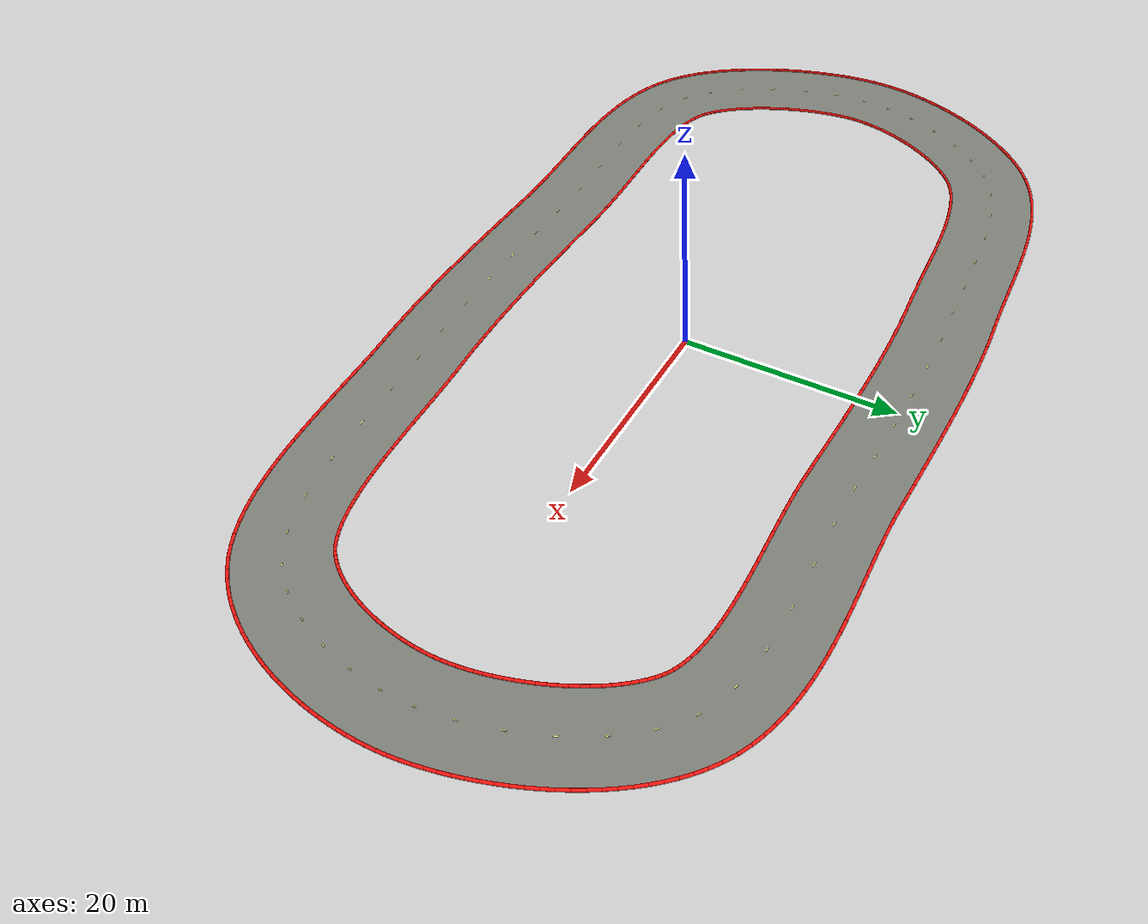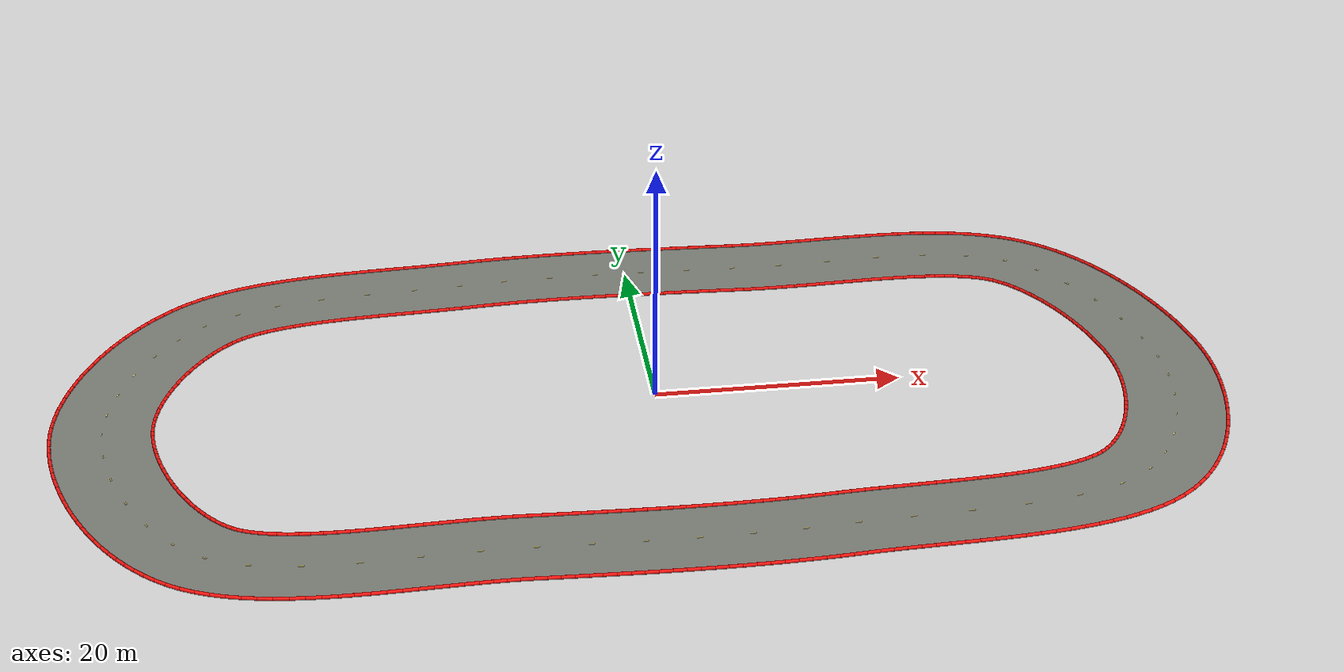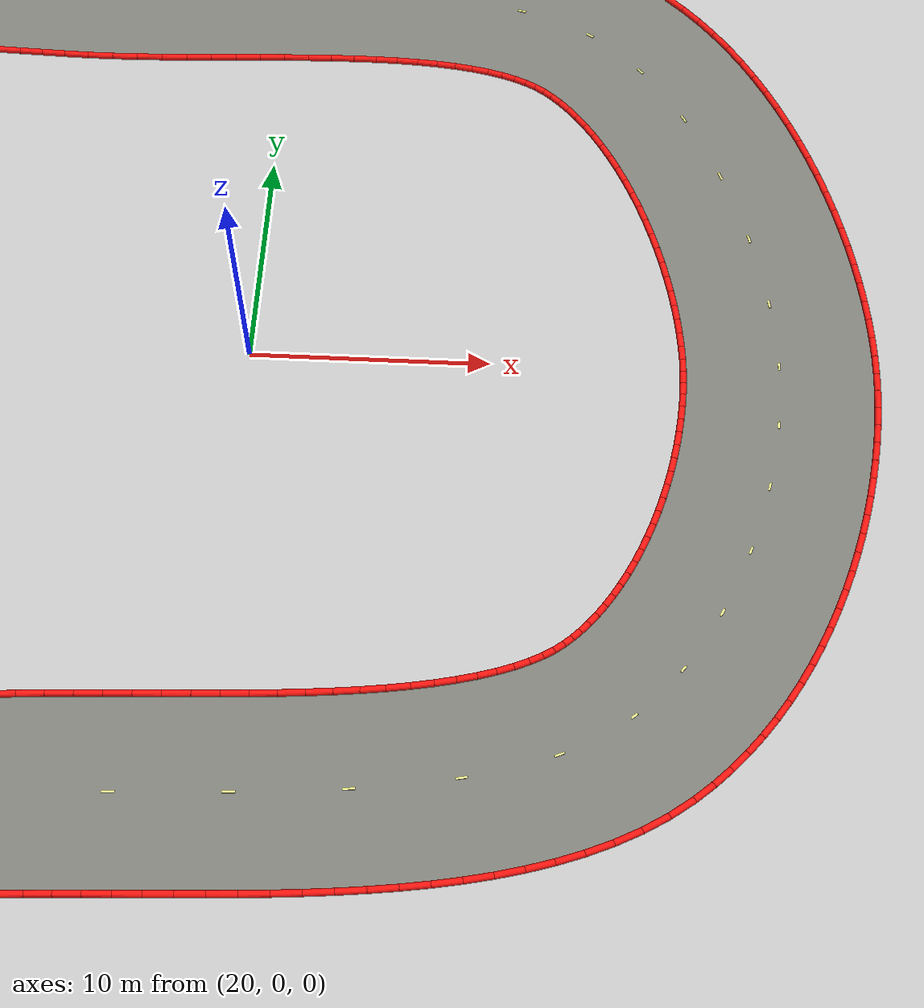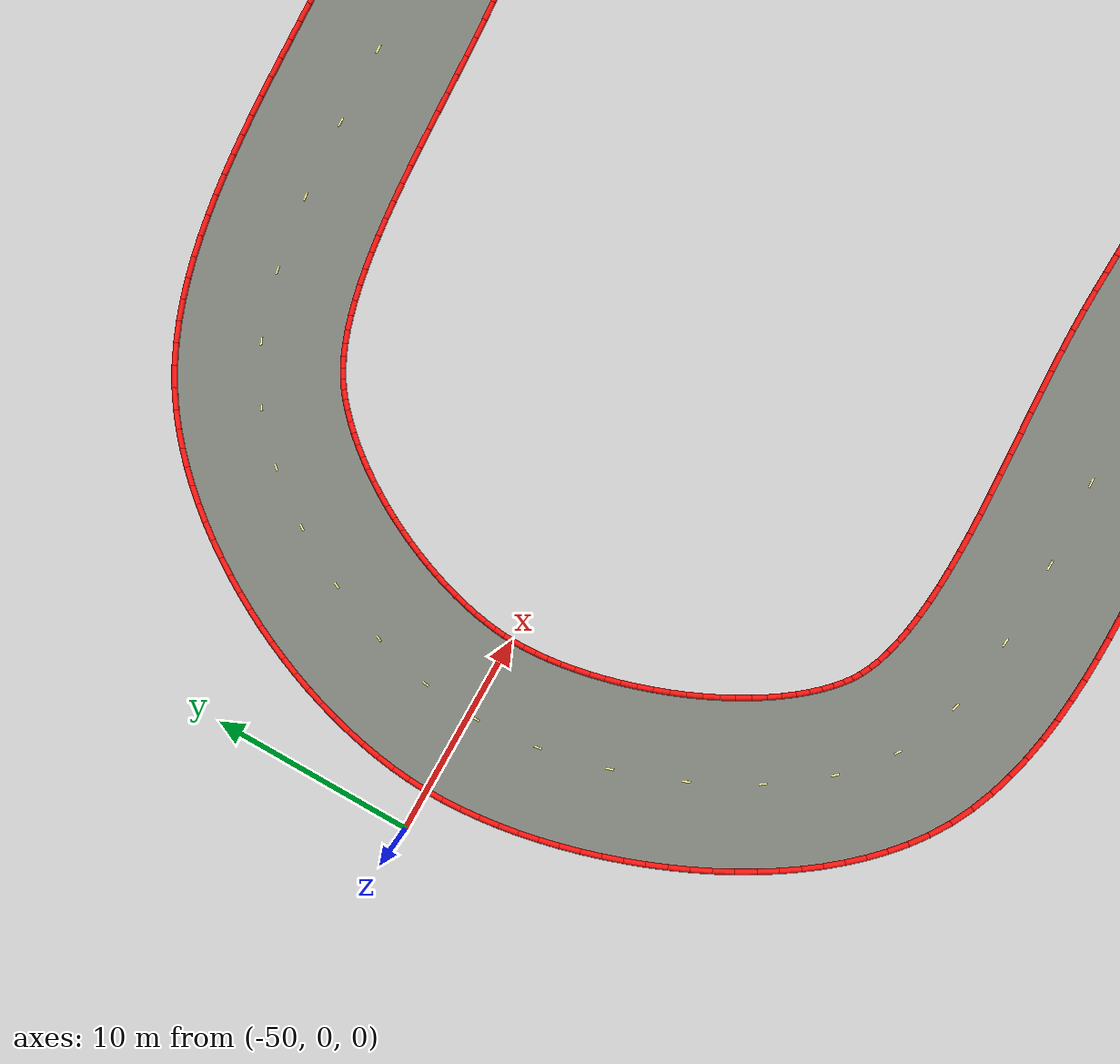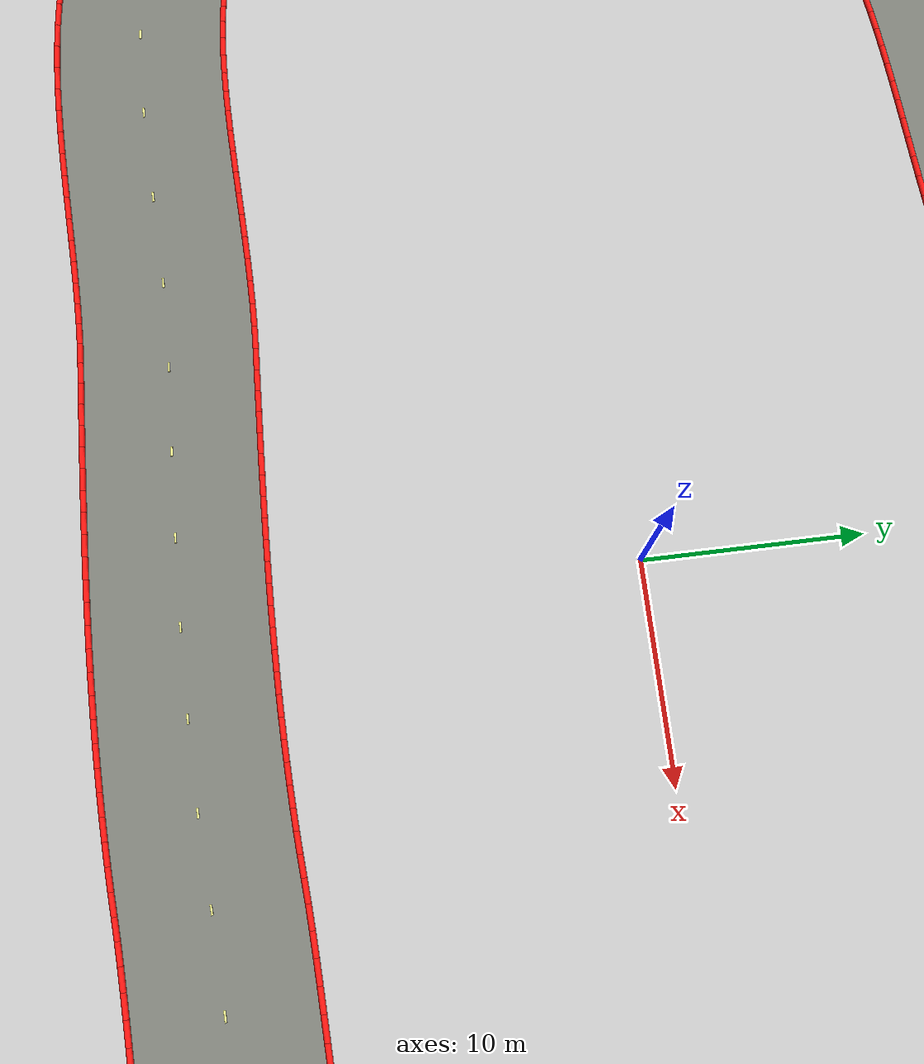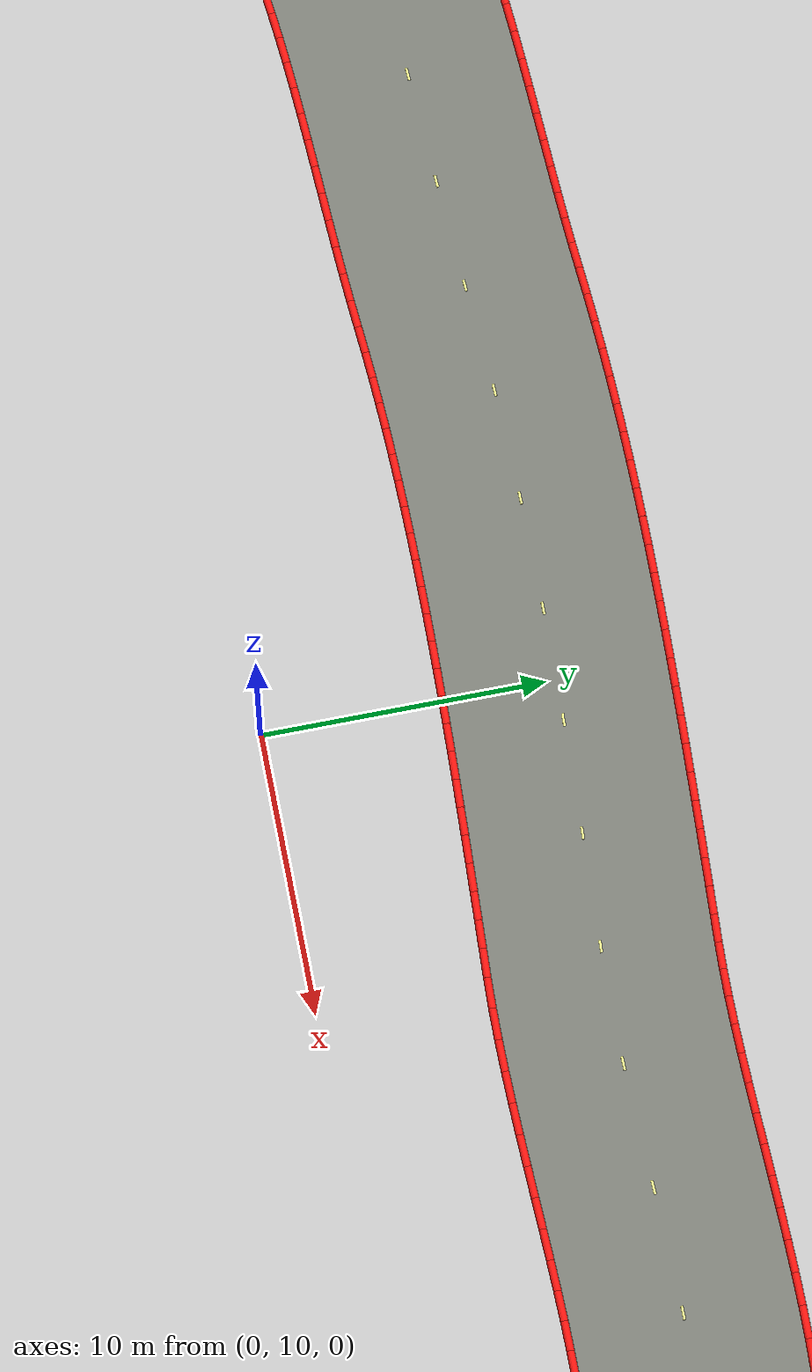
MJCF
<mujoco model="stop_go_track_visuals">
  <asset>
    <mesh name="track_surface_mesh" inertia="shell" vertex="38.00190 -0.12321 0.02200 37.97247 0.48079 0.02200 37.91867 1.11656 0.02200 37.83988 1.78425 0.02200 37.73601 2.47826 0.02200 37.60720 3.19328 0.02200 37.45376 3.92431 0.02200 37.27616 4.66652 0.02200 37.07495 5.41524 0.02200 36.85084 6.16591 0.02200 36.60461 6.91404 0.02200 36.33716 7.65520 0.02200 36.04951 8.38501 0.02200 35.74283 9.09909 0.02200 35.41846 9.79310 0.02200 35.07792 10.46271 0.02200 34.72297 11.10364 0.02200 34.35566 11.71163 0.02200 33.97833 12.28257 0.02200 33.59375 12.81247 0.02200 33.20504 13.29766 0.02200 32.81582 13.73488 0.02200 32.43006 14.12149 0.02200 32.05204 14.45578 0.02200 31.70280 14.72542 0.02200 31.30591 14.97986 0.02200 30.86646 15.20629 0.02200 30.35585 15.41864 0.02200 29.77335 15.61291 0.02200 29.12104 15.78548 0.02200 28.40291 15.93374 0.02200 27.62397 16.05625 0.02200 26.78975 16.15268 0.02200 25.90586 16.22364 0.02200 24.97782 16.27050 0.02200 24.01093 16.29524 0.02200 23.01024 16.30026 0.02200 21.98049 16.28830 0.02200 20.92618 16.26237 0.02200 19.85150 16.22565 0.02200 18.76042 16.18151 0.02200 17.65663 16.13341 0.02200 16.54360 16.08494 0.02200 15.42451 16.03979 0.02200 14.30230 16.00180 0.02200 13.17963 15.97491 0.02200 12.05884 15.96327 0.02200 10.94193 15.97126 0.02200 9.85879 16.00249 0.02200 8.83359 16.04513 0.02200 7.83297 16.08665 0.02200 6.83249 16.12753 0.02200 5.83242 16.16729 0.02200 4.83303 16.20545 0.02200 3.83460 16.24154 0.02200 2.83742 16.27509 0.02200 1.84175 16.30564 0.02200 0.84790 16.33271 0.02200 -0.14386 16.35586 0.02200 -1.13323 16.37461 0.02200 -2.11991 16.38852 0.02200 -3.10360 16.39713 0.02200 -4.08402 16.39998 0.02200 -5.06085 16.39664 0.02200 -6.03379 16.38666 0.02200 -7.00253 16.36961 0.02200 -7.96678 16.34504 0.02200 -8.92621 16.31254 0.02200 -9.88053 16.27167 0.02200 -10.82941 16.22201 0.02200 -11.77256 16.16315 0.02200 -12.70966 16.09468 0.02200 -13.66560 16.01400 0.02200 -14.63974 15.93277 0.02200 -15.64596 15.86012 0.02200 -16.65542 15.79568 0.02200 -17.66602 15.73684 0.02200 -18.67545 15.68112 0.02200 -19.68125 15.62611 0.02200 -20.68080 15.56951 0.02200 -21.67133 15.50907 0.02200 -22.64993 15.44264 0.02200 -23.61355 15.36816 0.02200 -24.55901 15.28369 0.02200 -25.48296 15.18739 0.02200 -26.38195 15.07758 0.02200 -27.25237 14.95280 0.02200 -28.09050 14.81180 0.02200 -28.89251 14.65364 0.02200 -29.65455 14.47775 0.02200 -30.37276 14.28399 0.02200 -31.04349 14.07272 0.02200 -31.66338 13.84488 0.02200 -32.22971 13.60195 0.02200 -32.74071 13.34585 0.02200 -33.19597 13.07872 0.02200 -33.61985 12.78521 0.02200 -33.99477 12.48706 0.02200 -34.39243 12.13776 0.02200 -34.79177 11.75230 0.02200 -35.18990 11.33259 0.02200 -35.58417 10.88083 0.02200 -35.97214 10.39941 0.02200 -36.35155 9.89089 0.02200 -36.72034 9.35791 0.02200 -37.07660 8.80320 0.02200 -37.41859 8.22956 0.02200 -37.74468 7.63983 0.02200 -38.05337 7.03692 0.02200 -38.34326 6.42376 0.02200 -38.61305 5.80336 0.02200 -38.86156 5.17875 0.02200 -39.08767 4.55305 0.02200 -39.29040 3.92945 0.02200 -39.46887 3.31121 0.02200 -39.62231 2.70171 0.02200 -39.75014 2.10443 0.02200 -39.85195 1.52295 0.02200 -39.92756 0.96100 0.02200 -39.97708 0.42244 0.02200 -40.00100 -0.08942 0.02200 -39.99993 -0.64143 0.02200 -39.97180 -1.23431 0.02200 -39.91560 -1.86553 0.02200 -39.83086 -2.52871 0.02200 -39.71757 -3.21790 0.02200 -39.57605 -3.92748 0.02200 -39.40686 -4.65215 0.02200 -39.21077 -5.38678 0.02200 -38.98869 -6.12646 0.02200 -38.74168 -6.86637 0.02200 -38.47092 -7.60181 0.02200 -38.17775 -8.32816 0.02200 -37.86364 -9.04083 0.02200 -37.53022 -9.73528 0.02200 -37.17933 -10.40702 0.02200 -36.81301 -11.05157 0.02200 -36.43358 -11.66452 0.02200 -36.04371 -12.24151 0.02200 -35.64640 -12.77835 0.02200 -35.24512 -13.27105 0.02200 -34.84380 -13.71595 0.02200 -34.44690 -14.10995 0.02200 -34.05930 -14.45074 0.02200 -33.70426 -14.72439 0.02200 -33.30591 -14.97986 0.02200 -32.86646 -15.20629 0.02200 -32.35585 -15.41864 0.02200 -31.77335 -15.61291 0.02200 -31.12104 -15.78548 0.02200 -30.40291 -15.93374 0.02200 -29.62397 -16.05625 0.02200 -28.78975 -16.15268 0.02200 -27.90586 -16.22364 0.02200 -26.97782 -16.27050 0.02200 -26.01093 -16.29524 0.02200 -25.01024 -16.30026 0.02200 -23.98049 -16.28830 0.02200 -22.92618 -16.26237 0.02200 -21.85150 -16.22565 0.02200 -20.76042 -16.18151 0.02200 -19.65663 -16.13341 0.02200 -18.54360 -16.08494 0.02200 -17.42451 -16.03979 0.02200 -16.30230 -16.00180 0.02200 -15.17963 -15.97491 0.02200 -14.05884 -15.96327 0.02200 -12.94193 -15.97126 0.02200 -11.85915 -16.00248 0.02200 -10.83583 -16.04486 0.02200 -9.83893 -16.08572 0.02200 -8.84338 -16.12562 0.02200 -7.84923 -16.16413 0.02200 -6.85652 -16.20082 0.02200 -5.86530 -16.23529 0.02200 -4.87561 -16.26712 0.02200 -3.88750 -16.29590 0.02200 -2.90101 -16.32121 0.02200 -1.91620 -16.34266 0.02200 -0.93312 -16.35983 0.02200 0.04821 -16.37232 0.02200 1.02771 -16.37974 0.02200 2.00536 -16.38168 0.02200 2.98110 -16.37774 0.02200 3.95488 -16.36754 0.02200 4.92667 -16.35067 0.02200 5.89642 -16.32675 0.02200 6.86408 -16.29540 0.02200 7.82962 -16.25622 0.02200 8.79300 -16.20884 0.02200 9.75417 -16.15287 0.02200 10.71312 -16.08793 0.02200 11.69592 -16.01157 0.02200 12.74636 -15.93305 0.02200 13.83830 -15.86584 0.02200 14.94087 -15.80895 0.02200 16.05120 -15.75931 0.02200 17.16610 -15.71402 0.02200 18.28214 -15.67026 0.02200 19.39563 -15.62534 0.02200 20.50271 -15.57663 0.02200 21.59929 -15.52159 0.02200 22.68110 -15.45779 0.02200 23.74365 -15.38288 0.02200 24.78227 -15.29469 0.02200 25.79204 -15.19120 0.02200 26.76784 -15.07064 0.02200 27.70429 -14.93153 0.02200 28.59579 -14.77279 0.02200 29.43650 -14.59391 0.02200 30.22049 -14.39502 0.02200 30.94181 -14.17715 0.02200 31.59482 -13.94240 0.02200 32.17463 -13.69405 0.02200 32.67782 -13.43658 0.02200 33.10335 -13.17526 0.02200 33.48239 -12.89168 0.02200 33.77607 -12.63197 0.02200 34.09195 -12.31774 0.02200 34.40592 -11.96732 0.02200 34.71593 -11.58155 0.02200 35.01992 -11.16180 0.02200 35.31593 -10.70988 0.02200 35.60216 -10.22791 0.02200 35.87697 -9.71828 0.02200 36.13893 -9.18357 0.02200 36.38678 -8.62648 0.02200 36.61944 -8.04979 0.02200 36.83599 -7.45635 0.02200 37.03563 -6.84908 0.02200 37.21772 -6.23091 0.02200 37.38170 -5.60479 0.02200 37.52715 -4.97373 0.02200 37.65371 -4.34074 0.02200 37.76113 -3.70888 0.02200 37.84925 -3.08124 0.02200 37.91800 -2.46100 0.02200 37.96742 -1.85136 0.02200 37.99764 -1.25565 0.02200 38.00895 -0.67729 0.02200 45.99810 0.12321 0.02200 45.95480 1.01224 0.02200 45.87804 1.92176 0.02200 45.76931 2.84457 0.02200 45.62952 3.77925 0.02200 45.45939 4.72404 0.02200 45.25943 5.67690 0.02200 45.03003 6.63563 0.02200 44.77146 7.59785 0.02200 44.48388 8.56107 0.02200 44.16733 9.52274 0.02200 43.82175 10.48024 0.02200 43.44697 11.43092 0.02200 43.04265 12.37211 0.02200 42.60831 13.30110 0.02200 42.14325 14.21519 0.02200 41.64657 15.11160 0.02200 41.11705 15.98755 0.02200 40.55319 16.84012 0.02200 39.95307 17.66623 0.02200 39.31439 18.46253 0.02200 38.63441 19.22524 0.02200 37.90997 19.94992 0.02200 37.13762 20.63129 0.02200 36.29720 21.27458 0.02200 35.30318 21.90963 0.02200 34.24823 22.45637 0.02200 33.16784 22.90815 0.02200 32.06964 23.27626 0.02200 30.95842 23.57162 0.02200 29.83710 23.80413 0.02200 28.70754 23.98253 0.02200 27.57112 24.11443 0.02200 26.42911 24.20651 0.02200 25.28287 24.26469 0.02200 24.13400 24.29430 0.02200 22.98434 24.30022 0.02200 21.83604 24.28699 0.02200 20.69149 24.25892 0.02200 19.55338 24.22010 0.02200 18.42464 24.17446 0.02200 17.30846 24.12583 0.02200 16.20827 24.07790 0.02200 15.12777 24.03429 0.02200 14.07092 23.99845 0.02200 13.04194 23.97372 0.02200 12.04538 23.96326 0.02200 11.08614 23.96996 0.02200 10.14121 23.99751 0.02200 9.16595 24.03822 0.02200 8.16211 24.07988 0.02200 7.15467 24.12104 0.02200 6.14392 24.16122 0.02200 5.13015 24.19993 0.02200 4.11361 24.23667 0.02200 3.09458 24.27096 0.02200 2.07334 24.30228 0.02200 1.05014 24.33016 0.02200 0.02525 24.35407 0.02200 -1.00107 24.37352 0.02200 -2.02856 24.38800 0.02200 -3.05698 24.39699 0.02200 -4.08606 24.39998 0.02200 -5.11557 24.39646 0.02200 -6.14524 24.38589 0.02200 -7.17485 24.36775 0.02200 -8.20413 24.34152 0.02200 -9.23286 24.30666 0.02200 -10.26078 24.26263 0.02200 -11.28766 24.20887 0.02200 -12.31325 24.14486 0.02200 -13.33731 24.07002 0.02200 -14.33440 23.98600 0.02200 -15.26035 23.90866 0.02200 -16.18864 23.84169 0.02200 -17.14262 23.78083 0.02200 -18.11892 23.72401 0.02200 -19.11435 23.66907 0.02200 -20.12589 23.61375 0.02200 -21.15067 23.55569 0.02200 -22.18599 23.49249 0.02200 -23.22925 23.42164 0.02200 -24.27803 23.34052 0.02200 -25.33003 23.24645 0.02200 -26.38310 23.13659 0.02200 -27.43522 23.00795 0.02200 -28.48450 22.85735 0.02200 -29.52919 22.68137 0.02200 -30.56762 22.47630 0.02200 -31.59817 22.23806 0.02200 -32.61919 21.96211 0.02200 -33.62888 21.64344 0.02200 -34.62509 21.27646 0.02200 -35.60505 20.85502 0.02200 -36.56506 20.37254 0.02200 -37.50004 19.82224 0.02200 -38.38015 19.21479 0.02200 -39.11922 18.63035 0.02200 -39.81008 18.02411 0.02200 -40.47198 17.38569 0.02200 -41.10595 16.71778 0.02200 -41.71282 16.02277 0.02200 -42.29321 15.30289 0.02200 -42.84753 14.56017 0.02200 -43.37602 13.79659 0.02200 -43.87874 13.01400 0.02200 -44.35562 12.21422 0.02200 -44.80645 11.39900 0.02200 -45.23090 10.57005 0.02200 -45.62854 9.72902 0.02200 -45.99882 8.87752 0.02200 -46.34111 8.01711 0.02200 -46.65468 7.14928 0.02200 -46.93869 6.27544 0.02200 -47.19219 5.39693 0.02200 -47.41411 4.51498 0.02200 -47.60320 3.63072 0.02200 -47.75804 2.74516 0.02200 -47.87698 1.85916 0.02200 -47.95808 0.97349 0.02200 -47.99900 0.08942 0.02200 -47.99755 -0.83672 0.02200 -47.95339 -1.77678 0.02200 -47.86918 -2.72609 0.02200 -47.74703 -3.68380 0.02200 -47.58859 -4.64866 0.02200 -47.39516 -5.61906 0.02200 -47.16783 -6.59311 0.02200 -46.90747 -7.56871 0.02200 -46.61480 -8.54357 0.02200 -46.29040 -9.51529 0.02200 -45.93472 -10.48136 0.02200 -45.54807 -11.43918 0.02200 -45.13061 -12.38614 0.02200 -44.68236 -13.31955 0.02200 -44.20311 -14.23671 0.02200 -43.69244 -15.13487 0.02200 -43.14968 -16.01124 0.02200 -42.57382 -16.86295 0.02200 -41.96346 -17.68700 0.02200 -41.31679 -18.48015 0.02200 -40.63151 -19.23885 0.02200 -39.90480 -19.95899 0.02200 -39.13342 -20.63567 0.02200 -38.29574 -21.27561 0.02200 -37.30318 -21.90963 0.02200 -36.24823 -22.45637 0.02200 -35.16784 -22.90815 0.02200 -34.06964 -23.27626 0.02200 -32.95842 -23.57162 0.02200 -31.83710 -23.80413 0.02200 -30.70754 -23.98253 0.02200 -29.57112 -24.11443 0.02200 -28.42911 -24.20651 0.02200 -27.28287 -24.26469 0.02200 -26.13400 -24.29430 0.02200 -24.98434 -24.30022 0.02200 -23.83604 -24.28699 0.02200 -22.69149 -24.25892 0.02200 -21.55338 -24.22010 0.02200 -20.42464 -24.17446 0.02200 -19.30846 -24.12583 0.02200 -18.20827 -24.07790 0.02200 -17.12777 -24.03429 0.02200 -16.07092 -23.99845 0.02200 -15.04194 -23.97372 0.02200 -14.04538 -23.96326 0.02200 -13.08614 -23.96996 0.02200 -12.14085 -23.99752 0.02200 -11.16548 -24.03806 0.02200 -10.16293 -24.07916 0.02200 -9.15835 -24.11942 0.02200 -8.15179 -24.15840 0.02200 -7.14328 -24.19568 0.02200 -6.13288 -24.23081 0.02200 -5.12062 -24.26337 0.02200 -4.10655 -24.29290 0.02200 -3.09071 -24.31896 0.02200 -2.07314 -24.34112 0.02200 -1.05388 -24.35892 0.02200 -0.03298 -24.37191 0.02200 0.98953 -24.37965 0.02200 2.01359 -24.38167 0.02200 3.03918 -24.37753 0.02200 4.06623 -24.36676 0.02200 5.09472 -24.34890 0.02200 6.12460 -24.32350 0.02200 7.15581 -24.29008 0.02200 8.18832 -24.24818 0.02200 9.22206 -24.19733 0.02200 10.25699 -24.13705 0.02200 11.29306 -24.06689 0.02200 12.30408 -23.98843 0.02200 13.29046 -23.91453 0.02200 14.28994 -23.85308 0.02200 15.32550 -23.79970 0.02200 16.39213 -23.75204 0.02200 17.48514 -23.70765 0.02200 18.60009 -23.66394 0.02200 19.73277 -23.61824 0.02200 20.87917 -23.56777 0.02200 22.03549 -23.50969 0.02200 23.19814 -23.44106 0.02200 24.36369 -23.35882 0.02200 25.52897 -23.25977 0.02200 26.69098 -23.14054 0.02200 27.84699 -22.99752 0.02200 28.99448 -22.82680 0.02200 30.13119 -22.62407 0.02200 31.25505 -22.38447 0.02200 32.36413 -22.10247 0.02200 33.45649 -21.77165 0.02200 34.52988 -21.38454 0.02200 35.58133 -20.93246 0.02200 36.60636 -20.40555 0.02200 37.59814 -19.79317 0.02200 38.51761 -19.10832 0.02200 39.23799 -18.47727 0.02200 39.89179 -17.82790 0.02200 40.50310 -17.14655 0.02200 41.07390 -16.43708 0.02200 41.60622 -15.70280 0.02200 42.10196 -14.94660 0.02200 42.56290 -14.17102 0.02200 42.99061 -13.37837 0.02200 43.38648 -12.57075 0.02200 43.75174 -11.75017 0.02200 44.08741 -10.91850 0.02200 44.39437 -10.07758 0.02200 44.67337 -9.22919 0.02200 44.92502 -8.37509 0.02200 45.14981 -7.51700 0.02200 45.34814 -6.65661 0.02200 45.52031 -5.79558 0.02200 45.66652 -4.93554 0.02200 45.78690 -4.07809 0.02200 45.88146 -3.22474 0.02200 45.95013 -2.37696 0.02200 45.99273 -1.53611 0.02200 46.00891 -0.70348 0.02200" face="0 241 1 0 240 241 1 242 2 1 241 242 2 243 3 2 242 243 3 244 4 3 243 244 4 245 5 4 244 245 5 246 6 5 245 246 6 247 7 6 246 247 7 248 8 7 247 248 8 249 9 8 248 249 9 250 10 9 249 250 10 251 11 10 250 251 11 252 12 11 251 252 12 253 13 12 252 253 13 254 14 13 253 254 14 255 15 14 254 255 15 256 16 15 255 256 16 257 17 16 256 257 17 258 18 17 257 258 18 259 19 18 258 259 19 260 20 19 259 260 20 261 21 20 260 261 21 262 22 21 261 262 22 263 23 22 262 263 23 264 24 23 263 264 24 265 25 24 264 265 25 266 26 25 265 266 26 267 27 26 266 267 27 268 28 27 267 268 28 269 29 28 268 269 29 270 30 29 269 270 30 271 31 30 270 271 31 272 32 31 271 272 32 273 33 32 272 273 33 274 34 33 273 274 34 275 35 34 274 275 35 276 36 35 275 276 36 277 37 36 276 277 37 278 38 37 277 278 38 279 39 38 278 279 39 280 40 39 279 280 40 281 41 40 280 281 41 282 42 41 281 282 42 283 43 42 282 283 43 284 44 43 283 284 44 285 45 44 284 285 45 286 46 45 285 286 46 287 47 46 286 287 47 288 48 47 287 288 48 289 49 48 288 289 49 290 50 49 289 290 50 291 51 50 290 291 51 292 52 51 291 292 52 293 53 52 292 293 53 294 54 53 293 294 54 295 55 54 294 295 55 296 56 55 295 296 56 297 57 56 296 297 57 298 58 57 297 298 58 299 59 58 298 299 59 300 60 59 299 300 60 301 61 60 300 301 61 302 62 61 301 302 62 303 63 62 302 303 63 304 64 63 303 304 64 305 65 64 304 305 65 306 66 65 305 306 66 307 67 66 306 307 67 308 68 67 307 308 68 309 69 68 308 309 69 310 70 69 309 310 70 311 71 70 310 311 71 312 72 71 311 312 72 313 73 72 312 313 73 314 74 73 313 314 74 315 75 74 314 315 75 316 76 75 315 316 76 317 77 76 316 317 77 318 78 77 317 318 78 319 79 78 318 319 79 320 80 79 319 320 80 321 81 80 320 321 81 322 82 81 321 322 82 323 83 82 322 323 83 324 84 83 323 324 84 325 85 84 324 325 85 326 86 85 325 326 86 327 87 86 326 327 87 328 88 87 327 328 88 329 89 88 328 329 89 330 90 89 329 330 90 331 91 90 330 331 91 332 92 91 331 332 92 333 93 92 332 333 93 334 94 93 333 334 94 335 95 94 334 335 95 336 96 95 335 336 96 337 97 96 336 337 97 338 98 97 337 338 98 339 99 98 338 339 99 340 100 99 339 340 100 341 101 100 340 341 101 342 102 101 341 342 102 343 103 102 342 343 103 344 104 103 343 344 104 345 105 104 344 345 105 346 106 105 345 346 106 347 107 106 346 347 107 348 108 107 347 348 108 349 109 108 348 349 109 350 110 109 349 350 110 351 111 110 350 351 111 352 112 111 351 352 112 353 113 112 352 353 113 354 114 113 353 354 114 355 115 114 354 355 115 356 116 115 355 356 116 357 117 116 356 357 117 358 118 117 357 358 118 359 119 118 358 359 119 360 120 119 359 360 120 361 121 120 360 361 121 362 122 121 361 362 122 363 123 122 362 363 123 364 124 123 363 364 124 365 125 124 364 365 125 366 126 125 365 366 126 367 127 126 366 367 127 368 128 127 367 368 128 369 129 128 368 369 129 370 130 129 369 370 130 371 131 130 370 371 131 372 132 131 371 372 132 373 133 132 372 373 133 374 134 133 373 374 134 375 135 134 374 375 135 376 136 135 375 376 136 377 137 136 376 377 137 378 138 137 377 378 138 379 139 138 378 379 139 380 140 139 379 380 140 381 141 140 380 381 141 382 142 141 381 382 142 383 143 142 382 383 143 384 144 143 383 384 144 385 145 144 384 385 145 386 146 145 385 386 146 387 147 146 386 387 147 388 148 147 387 388 148 389 149 148 388 389 149 390 150 149 389 390 150 391 151 150 390 391 151 392 152 151 391 392 152 393 153 152 392 393 153 394 154 153 393 394 154 395 155 154 394 395 155 396 156 155 395 396 156 397 157 156 396 397 157 398 158 157 397 398 158 399 159 158 398 399 159 400 160 159 399 400 160 401 161 160 400 401 161 402 162 161 401 402 162 403 163 162 402 403 163 404 164 163 403 404 164 405 165 164 404 405 165 406 166 165 405 406 166 407 167 166 406 407 167 408 168 167 407 408 168 409 169 168 408 409 169 410 170 169 409 410 170 411 171 170 410 411 171 412 172 171 411 412 172 413 173 172 412 413 173 414 174 173 413 414 174 415 175 174 414 415 175 416 176 175 415 416 176 417 177 176 416 417 177 418 178 177 417 418 178 419 179 178 418 419 179 420 180 179 419 420 180 421 181 180 420 421 181 422 182 181 421 422 182 423 183 182 422 423 183 424 184 183 423 424 184 425 185 184 424 425 185 426 186 185 425 426 186 427 187 186 426 427 187 428 188 187 427 428 188 429 189 188 428 429 189 430 190 189 429 430 190 431 191 190 430 431 191 432 192 191 431 432 192 433 193 192 432 433 193 434 194 193 433 434 194 435 195 194 434 435 195 436 196 195 435 436 196 437 197 196 436 437 197 438 198 197 437 438 198 439 199 198 438 439 199 440 200 199 439 440 200 441 201 200 440 441 201 442 202 201 441 442 202 443 203 202 442 443 203 444 204 203 443 444 204 445 205 204 444 445 205 446 206 205 445 446 206 447 207 206 446 447 207 448 208 207 447 448 208 449 209 208 448 449 209 450 210 209 449 450 210 451 211 210 450 451 211 452 212 211 451 452 212 453 213 212 452 453 213 454 214 213 453 454 214 455 215 214 454 455 215 456 216 215 455 456 216 457 217 216 456 457 217 458 218 217 457 458 218 459 219 218 458 459 219 460 220 219 459 460 220 461 221 220 460 461 221 462 222 221 461 462 222 463 223 222 462 463 223 464 224 223 463 464 224 465 225 224 464 465 225 466 226 225 465 466 226 467 227 226 466 467 227 468 228 227 467 468 228 469 229 228 468 469 229 470 230 229 469 470 230 471 231 230 470 471 231 472 232 231 471 472 232 473 233 232 472 473 233 474 234 233 473 474 234 475 235 234 474 475 235 476 236 235 475 476 236 477 237 236 476 477 237 478 238 237 477 478 238 479 239 238 478 479 239 240 0 239 479 240"/>
    <material name="track_asphalt" rgba="0.48 0.49 0.46 1" emission="0.08"/>
    <material name="track_boundary" rgba="0.95 0.08 0.06 1" emission="0.05"/>
    <material name="track_centerline" rgba="1.0 0.95 0.55 1" emission="0.15"/>
  </asset>
  <worldbody>
    <geom name="track_surface" type="mesh" mesh="track_surface_mesh" material="track_asphalt" contype="0" conaffinity="0"/>
    <geom name="track_left_boundary_000" type="capsule" fromto="38.00190 -0.12321 0.09 37.97247 0.48079 0.09" size="0.14" material="track_boundary" contype="0" conaffinity="0"/>
    <geom name="track_left_boundary_001" type="capsule" fromto="37.97247 0.48079 0.09 37.91867 1.11656 0.09" size="0.14" material="track_boundary" contype="0" conaffinity="0"/>
    <geom name="track_left_boundary_002" type="capsule" fromto="37.91867 1.11656 0.09 37.83988 1.78425 0.09" size="0.14" material="track_boundary" contype="0" conaffinity="0"/>
    <geom name="track_left_boundary_003" type="capsule" fromto="37.83988 1.78425 0.09 37.73601 2.47826 0.09" size="0.14" material="track_boundary" contype="0" conaffinity="0"/>
    <geom name="track_left_boundary_004" type="capsule" fromto="37.73601 2.47826 0.09 37.60720 3.19328 0.09" size="0.14" material="track_boundary" contype="0" conaffinity="0"/>
    <geom name="track_left_boundary_005" type="capsule" fromto="37.60720 3.19328 0.09 37.45376 3.92431 0.09" size="0.14" material="track_boundary" contype="0" conaffinity="0"/>
    <geom name="track_left_boundary_006" type="capsule" fromto="37.45376 3.92431 0.09 37.27616 4.66652 0.09" size="0.14" material="track_boundary" contype="0" conaffinity="0"/>
    <geom name="track_left_boundary_007" type="capsule" fromto="37.27616 4.66652 0.09 37.07495 5.41524 0.09" size="0.14" material="track_boundary" contype="0" conaffinity="0"/>
    <geom name="track_left_boundary_008" type="capsule" fromto="37.07495 5.41524 0.09 36.85084 6.16591 0.09" size="0.14" material="track_boundary" contype="0" conaffinity="0"/>
    <geom name="track_left_boundary_009" type="capsule" fromto="36.85084 6.16591 0.09 36.60461 6.91404 0.09" size="0.14" material="track_boundary" contype="0" conaffinity="0"/>
    <geom name="track_left_boundary_010" type="capsule" fromto="36.60461 6.91404 0.09 36.33716 7.65520 0.09" size="0.14" material="track_boundary" contype="0" conaffinity="0"/>
    <geom name="track_left_boundary_011" type="capsule" fromto="36.33716 7.65520 0.09 36.04951 8.38501 0.09" size="0.14" material="track_boundary" contype="0" conaffinity="0"/>
    <geom name="track_left_boundary_012" type="capsule" fromto="36.04951 8.38501 0.09 35.74283 9.09909 0.09" size="0.14" material="track_boundary" contype="0" conaffinity="0"/>
    <geom name="track_left_boundary_013" type="capsule" fromto="35.74283 9.09909 0.09 35.41846 9.79310 0.09" size="0.14" material="track_boundary" contype="0" conaffinity="0"/>
    <geom name="track_left_boundary_014" type="capsule" fromto="35.41846 9.79310 0.09 35.07792 10.46271 0.09" size="0.14" material="track_boundary" contype="0" conaffinity="0"/>
    <geom name="track_left_boundary_015" type="capsule" fromto="35.07792 10.46271 0.09 34.72297 11.10364 0.09" size="0.14" material="track_boundary" contype="0" conaffinity="0"/>
    <geom name="track_left_boundary_016" type="capsule" fromto="34.72297 11.10364 0.09 34.35566 11.71163 0.09" size="0.14" material="track_boundary" contype="0" conaffinity="0"/>
    <geom name="track_left_boundary_017" type="capsule" fromto="34.35566 11.71163 0.09 33.97833 12.28257 0.09" size="0.14" material="track_boundary" contype="0" conaffinity="0"/>
    <geom name="track_left_boundary_018" type="capsule" fromto="33.97833 12.28257 0.09 33.59375 12.81247 0.09" size="0.14" material="track_boundary" contype="0" conaffinity="0"/>
    <geom name="track_left_boundary_019" type="capsule" fromto="33.59375 12.81247 0.09 33.20504 13.29766 0.09" size="0.14" material="track_boundary" contype="0" conaffinity="0"/>
    <geom name="track_left_boundary_020" type="capsule" fromto="33.20504 13.29766 0.09 32.81582 13.73488 0.09" size="0.14" material="track_boundary" contype="0" conaffinity="0"/>
    <geom name="track_left_boundary_021" type="capsule" fromto="32.81582 13.73488 0.09 32.43006 14.12149 0.09" size="0.14" material="track_boundary" contype="0" conaffinity="0"/>
    <geom name="track_left_boundary_022" type="capsule" fromto="32.43006 14.12149 0.09 32.05204 14.45578 0.09" size="0.14" material="track_boundary" contype="0" conaffinity="0"/>
    <geom name="track_left_boundary_023" type="capsule" fromto="32.05204 14.45578 0.09 31.70280 14.72542 0.09" size="0.14" material="track_boundary" contype="0" conaffinity="0"/>
    <geom name="track_left_boundary_024" type="capsule" fromto="31.70280 14.72542 0.09 31.30591 14.97986 0.09" size="0.14" material="track_boundary" contype="0" conaffinity="0"/>
    <geom name="track_left_boundary_025" type="capsule" fromto="31.30591 14.97986 0.09 30.86646 15.20629 0.09" size="0.14" material="track_boundary" contype="0" conaffinity="0"/>
    <geom name="track_left_boundary_026" type="capsule" fromto="30.86646 15.20629 0.09 30.35585 15.41864 0.09" size="0.14" material="track_boundary" contype="0" conaffinity="0"/>
    <geom name="track_left_boundary_027" type="capsule" fromto="30.35585 15.41864 0.09 29.77335 15.61291 0.09" size="0.14" material="track_boundary" contype="0" conaffinity="0"/>
    <geom name="track_left_boundary_028" type="capsule" fromto="29.77335 15.61291 0.09 29.12104 15.78548 0.09" size="0.14" material="track_boundary" contype="0" conaffinity="0"/>
    <geom name="track_left_boundary_029" type="capsule" fromto="29.12104 15.78548 0.09 28.40291 15.93374 0.09" size="0.14" material="track_boundary" contype="0" conaffinity="0"/>
    <geom name="track_left_boundary_030" type="capsule" fromto="28.40291 15.93374 0.09 27.62397 16.05625 0.09" size="0.14" material="track_boundary" contype="0" conaffinity="0"/>
    <geom name="track_left_boundary_031" type="capsule" fromto="27.62397 16.05625 0.09 26.78975 16.15268 0.09" size="0.14" material="track_boundary" contype="0" conaffinity="0"/>
    <geom name="track_left_boundary_032" type="capsule" fromto="26.78975 16.15268 0.09 25.90586 16.22364 0.09" size="0.14" material="track_boundary" contype="0" conaffinity="0"/>
    <geom name="track_left_boundary_033" type="capsule" fromto="25.90586 16.22364 0.09 24.97782 16.27050 0.09" size="0.14" material="track_boundary" contype="0" conaffinity="0"/>
    <geom name="track_left_boundary_034" type="capsule" fromto="24.97782 16.27050 0.09 24.01093 16.29524 0.09" size="0.14" material="track_boundary" contype="0" conaffinity="0"/>
    <geom name="track_left_boundary_035" type="capsule" fromto="24.01093 16.29524 0.09 23.01024 16.30026 0.09" size="0.14" material="track_boundary" contype="0" conaffinity="0"/>
    <geom name="track_left_boundary_036" type="capsule" fromto="23.01024 16.30026 0.09 21.98049 16.28830 0.09" size="0.14" material="track_boundary" contype="0" conaffinity="0"/>
    <geom name="track_left_boundary_037" type="capsule" fromto="21.98049 16.28830 0.09 20.92618 16.26237 0.09" size="0.14" material="track_boundary" contype="0" conaffinity="0"/>
    <geom name="track_left_boundary_038" type="capsule" fromto="20.92618 16.26237 0.09 19.85150 16.22565 0.09" size="0.14" material="track_boundary" contype="0" conaffinity="0"/>
    <geom name="track_left_boundary_039" type="capsule" fromto="19.85150 16.22565 0.09 18.76042 16.18151 0.09" size="0.14" material="track_boundary" contype="0" conaffinity="0"/>
    <geom name="track_left_boundary_040" type="capsule" fromto="18.76042 16.18151 0.09 17.65663 16.13341 0.09" size="0.14" material="track_boundary" contype="0" conaffinity="0"/>
    <geom name="track_left_boundary_041" type="capsule" fromto="17.65663 16.13341 0.09 16.54360 16.08494 0.09" size="0.14" material="track_boundary" contype="0" conaffinity="0"/>
    <geom name="track_left_boundary_042" type="capsule" fromto="16.54360 16.08494 0.09 15.42451 16.03979 0.09" size="0.14" material="track_boundary" contype="0" conaffinity="0"/>
    <geom name="track_left_boundary_043" type="capsule" fromto="15.42451 16.03979 0.09 14.30230 16.00180 0.09" size="0.14" material="track_boundary" contype="0" conaffinity="0"/>
    <geom name="track_left_boundary_044" type="capsule" fromto="14.30230 16.00180 0.09 13.17963 15.97491 0.09" size="0.14" material="track_boundary" contype="0" conaffinity="0"/>
    <geom name="track_left_boundary_045" type="capsule" fromto="13.17963 15.97491 0.09 12.05884 15.96327 0.09" size="0.14" material="track_boundary" contype="0" conaffinity="0"/>
    <geom name="track_left_boundary_046" type="capsule" fromto="12.05884 15.96327 0.09 10.94193 15.97126 0.09" size="0.14" material="track_boundary" contype="0" conaffinity="0"/>
    <geom name="track_left_boundary_047" type="capsule" fromto="10.94193 15.97126 0.09 9.85879 16.00249 0.09" size="0.14" material="track_boundary" contype="0" conaffinity="0"/>
    <geom name="track_left_boundary_048" type="capsule" fromto="9.85879 16.00249 0.09 8.83359 16.04513 0.09" size="0.14" material="track_boundary" contype="0" conaffinity="0"/>
    <geom name="track_left_boundary_049" type="capsule" fromto="8.83359 16.04513 0.09 7.83297 16.08665 0.09" size="0.14" material="track_boundary" contype="0" conaffinity="0"/>
    <geom name="track_left_boundary_050" type="capsule" fromto="7.83297 16.08665 0.09 6.83249 16.12753 0.09" size="0.14" material="track_boundary" contype="0" conaffinity="0"/>
    <geom name="track_left_boundary_051" type="capsule" fromto="6.83249 16.12753 0.09 5.83242 16.16729 0.09" size="0.14" material="track_boundary" contype="0" conaffinity="0"/>
    <geom name="track_left_boundary_052" type="capsule" fromto="5.83242 16.16729 0.09 4.83303 16.20545 0.09" size="0.14" material="track_boundary" contype="0" conaffinity="0"/>
    <geom name="track_left_boundary_053" type="capsule" fromto="4.83303 16.20545 0.09 3.83460 16.24154 0.09" size="0.14" material="track_boundary" contype="0" conaffinity="0"/>
    <geom name="track_left_boundary_054" type="capsule" fromto="3.83460 16.24154 0.09 2.83742 16.27509 0.09" size="0.14" material="track_boundary" contype="0" conaffinity="0"/>
    <geom name="track_left_boundary_055" type="capsule" fromto="2.83742 16.27509 0.09 1.84175 16.30564 0.09" size="0.14" material="track_boundary" contype="0" conaffinity="0"/>
    <geom name="track_left_boundary_056" type="capsule" fromto="1.84175 16.30564 0.09 0.84790 16.33271 0.09" size="0.14" material="track_boundary" contype="0" conaffinity="0"/>
    <geom name="track_left_boundary_057" type="capsule" fromto="0.84790 16.33271 0.09 -0.14386 16.35586 0.09" size="0.14" material="track_boundary" contype="0" conaffinity="0"/>
    <geom name="track_left_boundary_058" type="capsule" fromto="-0.14386 16.35586 0.09 -1.13323 16.37461 0.09" size="0.14" material="track_boundary" contype="0" conaffinity="0"/>
    <geom name="track_left_boundary_059" type="capsule" fromto="-1.13323 16.37461 0.09 -2.11991 16.38852 0.09" size="0.14" material="track_boundary" contype="0" conaffinity="0"/>
    <geom name="track_left_boundary_060" type="capsule" fromto="-2.11991 16.38852 0.09 -3.10360 16.39713 0.09" size="0.14" material="track_boundary" contype="0" conaffinity="0"/>
    <geom name="track_left_boundary_061" type="capsule" fromto="-3.10360 16.39713 0.09 -4.08402 16.39998 0.09" size="0.14" material="track_boundary" contype="0" conaffinity="0"/>
    <geom name="track_left_boundary_062" type="capsule" fromto="-4.08402 16.39998 0.09 -5.06085 16.39664 0.09" size="0.14" material="track_boundary" contype="0" conaffinity="0"/>
    <geom name="track_left_boundary_063" type="capsule" fromto="-5.06085 16.39664 0.09 -6.03379 16.38666 0.09" size="0.14" material="track_boundary" contype="0" conaffinity="0"/>
    <geom name="track_left_boundary_064" type="capsule" fromto="-6.03379 16.38666 0.09 -7.00253 16.36961 0.09" size="0.14" material="track_boundary" contype="0" conaffinity="0"/>
    <geom name="track_left_boundary_065" type="capsule" fromto="-7.00253 16.36961 0.09 -7.96678 16.34504 0.09" size="0.14" material="track_boundary" contype="0" conaffinity="0"/>
    <geom name="track_left_boundary_066" type="capsule" fromto="-7.96678 16.34504 0.09 -8.92621 16.31254 0.09" size="0.14" material="track_boundary" contype="0" conaffinity="0"/>
    <geom name="track_left_boundary_067" type="capsule" fromto="-8.92621 16.31254 0.09 -9.88053 16.27167 0.09" size="0.14" material="track_boundary" contype="0" conaffinity="0"/>
    <geom name="track_left_boundary_068" type="capsule" fromto="-9.88053 16.27167 0.09 -10.82941 16.22201 0.09" size="0.14" material="track_boundary" contype="0" conaffinity="0"/>
    <geom name="track_left_boundary_069" type="capsule" fromto="-10.82941 16.22201 0.09 -11.77256 16.16315 0.09" size="0.14" material="track_boundary" contype="0" conaffinity="0"/>
    <geom name="track_left_boundary_070" type="capsule" fromto="-11.77256 16.16315 0.09 -12.70966 16.09468 0.09" size="0.14" material="track_boundary" contype="0" conaffinity="0"/>
    <geom name="track_left_boundary_071" type="capsule" fromto="-12.70966 16.09468 0.09 -13.66560 16.01400 0.09" size="0.14" material="track_boundary" contype="0" conaffinity="0"/>
    <geom name="track_left_boundary_072" type="capsule" fromto="-13.66560 16.01400 0.09 -14.63974 15.93277 0.09" size="0.14" material="track_boundary" contype="0" conaffinity="0"/>
    <geom name="track_left_boundary_073" type="capsule" fromto="-14.63974 15.93277 0.09 -15.64596 15.86012 0.09" size="0.14" material="track_boundary" contype="0" conaffinity="0"/>
    <geom name="track_left_boundary_074" type="capsule" fromto="-15.64596 15.86012 0.09 -16.65542 15.79568 0.09" size="0.14" material="track_boundary" contype="0" conaffinity="0"/>
    <geom name="track_left_boundary_075" type="capsule" fromto="-16.65542 15.79568 0.09 -17.66602 15.73684 0.09" size="0.14" material="track_boundary" contype="0" conaffinity="0"/>
    <geom name="track_left_boundary_076" type="capsule" fromto="-17.66602 15.73684 0.09 -18.67545 15.68112 0.09" size="0.14" material="track_boundary" contype="0" conaffinity="0"/>
    <geom name="track_left_boundary_077" type="capsule" fromto="-18.67545 15.68112 0.09 -19.68125 15.62611 0.09" size="0.14" material="track_boundary" contype="0" conaffinity="0"/>
    <geom name="track_left_boundary_078" type="capsule" fromto="-19.68125 15.62611 0.09 -20.68080 15.56951 0.09" size="0.14" material="track_boundary" contype="0" conaffinity="0"/>
    <geom name="track_left_boundary_079" type="capsule" fromto="-20.68080 15.56951 0.09 -21.67133 15.50907 0.09" size="0.14" material="track_boundary" contype="0" conaffinity="0"/>
    <geom name="track_left_boundary_080" type="capsule" fromto="-21.67133 15.50907 0.09 -22.64993 15.44264 0.09" size="0.14" material="track_boundary" contype="0" conaffinity="0"/>
    <geom name="track_left_boundary_081" type="capsule" fromto="-22.64993 15.44264 0.09 -23.61355 15.36816 0.09" size="0.14" material="track_boundary" contype="0" conaffinity="0"/>
    <geom name="track_left_boundary_082" type="capsule" fromto="-23.61355 15.36816 0.09 -24.55901 15.28369 0.09" size="0.14" material="track_boundary" contype="0" conaffinity="0"/>
    <geom name="track_left_boundary_083" type="capsule" fromto="-24.55901 15.28369 0.09 -25.48296 15.18739 0.09" size="0.14" material="track_boundary" contype="0" conaffinity="0"/>
    <geom name="track_left_boundary_084" type="capsule" fromto="-25.48296 15.18739 0.09 -26.38195 15.07758 0.09" size="0.14" material="track_boundary" contype="0" conaffinity="0"/>
    <geom name="track_left_boundary_085" type="capsule" fromto="-26.38195 15.07758 0.09 -27.25237 14.95280 0.09" size="0.14" material="track_boundary" contype="0" conaffinity="0"/>
    <geom name="track_left_boundary_086" type="capsule" fromto="-27.25237 14.95280 0.09 -28.09050 14.81180 0.09" size="0.14" material="track_boundary" contype="0" conaffinity="0"/>
    <geom name="track_left_boundary_087" type="capsule" fromto="-28.09050 14.81180 0.09 -28.89251 14.65364 0.09" size="0.14" material="track_boundary" contype="0" conaffinity="0"/>
    <geom name="track_left_boundary_088" type="capsule" fromto="-28.89251 14.65364 0.09 -29.65455 14.47775 0.09" size="0.14" material="track_boundary" contype="0" conaffinity="0"/>
    <geom name="track_left_boundary_089" type="capsule" fromto="-29.65455 14.47775 0.09 -30.37276 14.28399 0.09" size="0.14" material="track_boundary" contype="0" conaffinity="0"/>
    <geom name="track_left_boundary_090" type="capsule" fromto="-30.37276 14.28399 0.09 -31.04349 14.07272 0.09" size="0.14" material="track_boundary" contype="0" conaffinity="0"/>
    <geom name="track_left_boundary_091" type="capsule" fromto="-31.04349 14.07272 0.09 -31.66338 13.84488 0.09" size="0.14" material="track_boundary" contype="0" conaffinity="0"/>
    <geom name="track_left_boundary_092" type="capsule" fromto="-31.66338 13.84488 0.09 -32.22971 13.60195 0.09" size="0.14" material="track_boundary" contype="0" conaffinity="0"/>
    <geom name="track_left_boundary_093" type="capsule" fromto="-32.22971 13.60195 0.09 -32.74071 13.34585 0.09" size="0.14" material="track_boundary" contype="0" conaffinity="0"/>
    <geom name="track_left_boundary_094" type="capsule" fromto="-32.74071 13.34585 0.09 -33.19597 13.07872 0.09" size="0.14" material="track_boundary" contype="0" conaffinity="0"/>
    <geom name="track_left_boundary_095" type="capsule" fromto="-33.19597 13.07872 0.09 -33.61985 12.78521 0.09" size="0.14" material="track_boundary" contype="0" conaffinity="0"/>
    <geom name="track_left_boundary_096" type="capsule" fromto="-33.61985 12.78521 0.09 -33.99477 12.48706 0.09" size="0.14" material="track_boundary" contype="0" conaffinity="0"/>
    <geom name="track_left_boundary_097" type="capsule" fromto="-33.99477 12.48706 0.09 -34.39243 12.13776 0.09" size="0.14" material="track_boundary" contype="0" conaffinity="0"/>
    <geom name="track_left_boundary_098" type="capsule" fromto="-34.39243 12.13776 0.09 -34.79177 11.75230 0.09" size="0.14" material="track_boundary" contype="0" conaffinity="0"/>
    <geom name="track_left_boundary_099" type="capsule" fromto="-34.79177 11.75230 0.09 -35.18990 11.33259 0.09" size="0.14" material="track_boundary" contype="0" conaffinity="0"/>
    <geom name="track_left_boundary_100" type="capsule" fromto="-35.18990 11.33259 0.09 -35.58417 10.88083 0.09" size="0.14" material="track_boundary" contype="0" conaffinity="0"/>
    <geom name="track_left_boundary_101" type="capsule" fromto="-35.58417 10.88083 0.09 -35.97214 10.39941 0.09" size="0.14" material="track_boundary" contype="0" conaffinity="0"/>
    <geom name="track_left_boundary_102" type="capsule" fromto="-35.97214 10.39941 0.09 -36.35155 9.89089 0.09" size="0.14" material="track_boundary" contype="0" conaffinity="0"/>
    <geom name="track_left_boundary_103" type="capsule" fromto="-36.35155 9.89089 0.09 -36.72034 9.35791 0.09" size="0.14" material="track_boundary" contype="0" conaffinity="0"/>
    <geom name="track_left_boundary_104" type="capsule" fromto="-36.72034 9.35791 0.09 -37.07660 8.80320 0.09" size="0.14" material="track_boundary" contype="0" conaffinity="0"/>
    <geom name="track_left_boundary_105" type="capsule" fromto="-37.07660 8.80320 0.09 -37.41859 8.22956 0.09" size="0.14" material="track_boundary" contype="0" conaffinity="0"/>
    <geom name="track_left_boundary_106" type="capsule" fromto="-37.41859 8.22956 0.09 -37.74468 7.63983 0.09" size="0.14" material="track_boundary" contype="0" conaffinity="0"/>
    <geom name="track_left_boundary_107" type="capsule" fromto="-37.74468 7.63983 0.09 -38.05337 7.03692 0.09" size="0.14" material="track_boundary" contype="0" conaffinity="0"/>
    <geom name="track_left_boundary_108" type="capsule" fromto="-38.05337 7.03692 0.09 -38.34326 6.42376 0.09" size="0.14" material="track_boundary" contype="0" conaffinity="0"/>
    <geom name="track_left_boundary_109" type="capsule" fromto="-38.34326 6.42376 0.09 -38.61305 5.80336 0.09" size="0.14" material="track_boundary" contype="0" conaffinity="0"/>
    <geom name="track_left_boundary_110" type="capsule" fromto="-38.61305 5.80336 0.09 -38.86156 5.17875 0.09" size="0.14" material="track_boundary" contype="0" conaffinity="0"/>
    <geom name="track_left_boundary_111" type="capsule" fromto="-38.86156 5.17875 0.09 -39.08767 4.55305 0.09" size="0.14" material="track_boundary" contype="0" conaffinity="0"/>
    <geom name="track_left_boundary_112" type="capsule" fromto="-39.08767 4.55305 0.09 -39.29040 3.92945 0.09" size="0.14" material="track_boundary" contype="0" conaffinity="0"/>
    <geom name="track_left_boundary_113" type="capsule" fromto="-39.29040 3.92945 0.09 -39.46887 3.31121 0.09" size="0.14" material="track_boundary" contype="0" conaffinity="0"/>
    <geom name="track_left_boundary_114" type="capsule" fromto="-39.46887 3.31121 0.09 -39.62231 2.70171 0.09" size="0.14" material="track_boundary" contype="0" conaffinity="0"/>
    <geom name="track_left_boundary_115" type="capsule" fromto="-39.62231 2.70171 0.09 -39.75014 2.10443 0.09" size="0.14" material="track_boundary" contype="0" conaffinity="0"/>
    <geom name="track_left_boundary_116" type="capsule" fromto="-39.75014 2.10443 0.09 -39.85195 1.52295 0.09" size="0.14" material="track_boundary" contype="0" conaffinity="0"/>
    <geom name="track_left_boundary_117" type="capsule" fromto="-39.85195 1.52295 0.09 -39.92756 0.96100 0.09" size="0.14" material="track_boundary" contype="0" conaffinity="0"/>
    <geom name="track_left_boundary_118" type="capsule" fromto="-39.92756 0.96100 0.09 -39.97708 0.42244 0.09" size="0.14" material="track_boundary" contype="0" conaffinity="0"/>
    <geom name="track_left_boundary_119" type="capsule" fromto="-39.97708 0.42244 0.09 -40.00100 -0.08942 0.09" size="0.14" material="track_boundary" contype="0" conaffinity="0"/>
    <geom name="track_left_boundary_120" type="capsule" fromto="-40.00100 -0.08942 0.09 -39.99993 -0.64143 0.09" size="0.14" material="track_boundary" contype="0" conaffinity="0"/>
    <geom name="track_left_boundary_121" type="capsule" fromto="-39.99993 -0.64143 0.09 -39.97180 -1.23431 0.09" size="0.14" material="track_boundary" contype="0" conaffinity="0"/>
    <geom name="track_left_boundary_122" type="capsule" fromto="-39.97180 -1.23431 0.09 -39.91560 -1.86553 0.09" size="0.14" material="track_boundary" contype="0" conaffinity="0"/>
    <geom name="track_left_boundary_123" type="capsule" fromto="-39.91560 -1.86553 0.09 -39.83086 -2.52871 0.09" size="0.14" material="track_boundary" contype="0" conaffinity="0"/>
    <geom name="track_left_boundary_124" type="capsule" fromto="-39.83086 -2.52871 0.09 -39.71757 -3.21790 0.09" size="0.14" material="track_boundary" contype="0" conaffinity="0"/>
    <geom name="track_left_boundary_125" type="capsule" fromto="-39.71757 -3.21790 0.09 -39.57605 -3.92748 0.09" size="0.14" material="track_boundary" contype="0" conaffinity="0"/>
    <geom name="track_left_boundary_126" type="capsule" fromto="-39.57605 -3.92748 0.09 -39.40686 -4.65215 0.09" size="0.14" material="track_boundary" contype="0" conaffinity="0"/>
    <geom name="track_left_boundary_127" type="capsule" fromto="-39.40686 -4.65215 0.09 -39.21077 -5.38678 0.09" size="0.14" material="track_boundary" contype="0" conaffinity="0"/>
    <geom name="track_left_boundary_128" type="capsule" fromto="-39.21077 -5.38678 0.09 -38.98869 -6.12646 0.09" size="0.14" material="track_boundary" contype="0" conaffinity="0"/>
    <geom name="track_left_boundary_129" type="capsule" fromto="-38.98869 -6.12646 0.09 -38.74168 -6.86637 0.09" size="0.14" material="track_boundary" contype="0" conaffinity="0"/>
    <geom name="track_left_boundary_130" type="capsule" fromto="-38.74168 -6.86637 0.09 -38.47092 -7.60181 0.09" size="0.14" material="track_boundary" contype="0" conaffinity="0"/>
    <geom name="track_left_boundary_131" type="capsule" fromto="-38.47092 -7.60181 0.09 -38.17775 -8.32816 0.09" size="0.14" material="track_boundary" contype="0" conaffinity="0"/>
    <geom name="track_left_boundary_132" type="capsule" fromto="-38.17775 -8.32816 0.09 -37.86364 -9.04083 0.09" size="0.14" material="track_boundary" contype="0" conaffinity="0"/>
    <geom name="track_left_boundary_133" type="capsule" fromto="-37.86364 -9.04083 0.09 -37.53022 -9.73528 0.09" size="0.14" material="track_boundary" contype="0" conaffinity="0"/>
    <geom name="track_left_boundary_134" type="capsule" fromto="-37.53022 -9.73528 0.09 -37.17933 -10.40702 0.09" size="0.14" material="track_boundary" contype="0" conaffinity="0"/>
    <geom name="track_left_boundary_135" type="capsule" fromto="-37.17933 -10.40702 0.09 -36.81301 -11.05157 0.09" size="0.14" material="track_boundary" contype="0" conaffinity="0"/>
    <geom name="track_left_boundary_136" type="capsule" fromto="-36.81301 -11.05157 0.09 -36.43358 -11.66452 0.09" size="0.14" material="track_boundary" contype="0" conaffinity="0"/>
    <geom name="track_left_boundary_137" type="capsule" fromto="-36.43358 -11.66452 0.09 -36.04371 -12.24151 0.09" size="0.14" material="track_boundary" contype="0" conaffinity="0"/>
    <geom name="track_left_boundary_138" type="capsule" fromto="-36.04371 -12.24151 0.09 -35.64640 -12.77835 0.09" size="0.14" material="track_boundary" contype="0" conaffinity="0"/>
    <geom name="track_left_boundary_139" type="capsule" fromto="-35.64640 -12.77835 0.09 -35.24512 -13.27105 0.09" size="0.14" material="track_boundary" contype="0" conaffinity="0"/>
    <geom name="track_left_boundary_140" type="capsule" fromto="-35.24512 -13.27105 0.09 -34.84380 -13.71595 0.09" size="0.14" material="track_boundary" contype="0" conaffinity="0"/>
    <geom name="track_left_boundary_141" type="capsule" fromto="-34.84380 -13.71595 0.09 -34.44690 -14.10995 0.09" size="0.14" material="track_boundary" contype="0" conaffinity="0"/>
    <geom name="track_left_boundary_142" type="capsule" fromto="-34.44690 -14.10995 0.09 -34.05930 -14.45074 0.09" size="0.14" material="track_boundary" contype="0" conaffinity="0"/>
    <geom name="track_left_boundary_143" type="capsule" fromto="-34.05930 -14.45074 0.09 -33.70426 -14.72439 0.09" size="0.14" material="track_boundary" contype="0" conaffinity="0"/>
    <geom name="track_left_boundary_144" type="capsule" fromto="-33.70426 -14.72439 0.09 -33.30591 -14.97986 0.09" size="0.14" material="track_boundary" contype="0" conaffinity="0"/>
    <geom name="track_left_boundary_145" type="capsule" fromto="-33.30591 -14.97986 0.09 -32.86646 -15.20629 0.09" size="0.14" material="track_boundary" contype="0" conaffinity="0"/>
    <geom name="track_left_boundary_146" type="capsule" fromto="-32.86646 -15.20629 0.09 -32.35585 -15.41864 0.09" size="0.14" material="track_boundary" contype="0" conaffinity="0"/>
    <geom name="track_left_boundary_147" type="capsule" fromto="-32.35585 -15.41864 0.09 -31.77335 -15.61291 0.09" size="0.14" material="track_boundary" contype="0" conaffinity="0"/>
    <geom name="track_left_boundary_148" type="capsule" fromto="-31.77335 -15.61291 0.09 -31.12104 -15.78548 0.09" size="0.14" material="track_boundary" contype="0" conaffinity="0"/>
    <geom name="track_left_boundary_149" type="capsule" fromto="-31.12104 -15.78548 0.09 -30.40291 -15.93374 0.09" size="0.14" material="track_boundary" contype="0" conaffinity="0"/>
    <geom name="track_left_boundary_150" type="capsule" fromto="-30.40291 -15.93374 0.09 -29.62397 -16.05625 0.09" size="0.14" material="track_boundary" contype="0" conaffinity="0"/>
    <geom name="track_left_boundary_151" type="capsule" fromto="-29.62397 -16.05625 0.09 -28.78975 -16.15268 0.09" size="0.14" material="track_boundary" contype="0" conaffinity="0"/>
    <geom name="track_left_boundary_152" type="capsule" fromto="-28.78975 -16.15268 0.09 -27.90586 -16.22364 0.09" size="0.14" material="track_boundary" contype="0" conaffinity="0"/>
    <geom name="track_left_boundary_153" type="capsule" fromto="-27.90586 -16.22364 0.09 -26.97782 -16.27050 0.09" size="0.14" material="track_boundary" contype="0" conaffinity="0"/>
    <geom name="track_left_boundary_154" type="capsule" fromto="-26.97782 -16.27050 0.09 -26.01093 -16.29524 0.09" size="0.14" material="track_boundary" contype="0" conaffinity="0"/>
    <geom name="track_left_boundary_155" type="capsule" fromto="-26.01093 -16.29524 0.09 -25.01024 -16.30026 0.09" size="0.14" material="track_boundary" contype="0" conaffinity="0"/>
    <geom name="track_left_boundary_156" type="capsule" fromto="-25.01024 -16.30026 0.09 -23.98049 -16.28830 0.09" size="0.14" material="track_boundary" contype="0" conaffinity="0"/>
    <geom name="track_left_boundary_157" type="capsule" fromto="-23.98049 -16.28830 0.09 -22.92618 -16.26237 0.09" size="0.14" material="track_boundary" contype="0" conaffinity="0"/>
    <geom name="track_left_boundary_158" type="capsule" fromto="-22.92618 -16.26237 0.09 -21.85150 -16.22565 0.09" size="0.14" material="track_boundary" contype="0" conaffinity="0"/>
    <geom name="track_left_boundary_159" type="capsule" fromto="-21.85150 -16.22565 0.09 -20.76042 -16.18151 0.09" size="0.14" material="track_boundary" contype="0" conaffinity="0"/>
    <geom name="track_left_boundary_160" type="capsule" fromto="-20.76042 -16.18151 0.09 -19.65663 -16.13341 0.09" size="0.14" material="track_boundary" contype="0" conaffinity="0"/>
    <geom name="track_left_boundary_161" type="capsule" fromto="-19.65663 -16.13341 0.09 -18.54360 -16.08494 0.09" size="0.14" material="track_boundary" contype="0" conaffinity="0"/>
    <geom name="track_left_boundary_162" type="capsule" fromto="-18.54360 -16.08494 0.09 -17.42451 -16.03979 0.09" size="0.14" material="track_boundary" contype="0" conaffinity="0"/>
    <geom name="track_left_boundary_163" type="capsule" fromto="-17.42451 -16.03979 0.09 -16.30230 -16.00180 0.09" size="0.14" material="track_boundary" contype="0" conaffinity="0"/>
    <geom name="track_left_boundary_164" type="capsule" fromto="-16.30230 -16.00180 0.09 -15.17963 -15.97491 0.09" size="0.14" material="track_boundary" contype="0" conaffinity="0"/>
    <geom name="track_left_boundary_165" type="capsule" fromto="-15.17963 -15.97491 0.09 -14.05884 -15.96327 0.09" size="0.14" material="track_boundary" contype="0" conaffinity="0"/>
    <geom name="track_left_boundary_166" type="capsule" fromto="-14.05884 -15.96327 0.09 -12.94193 -15.97126 0.09" size="0.14" material="track_boundary" contype="0" conaffinity="0"/>
    <geom name="track_left_boundary_167" type="capsule" fromto="-12.94193 -15.97126 0.09 -11.85915 -16.00248 0.09" size="0.14" material="track_boundary" contype="0" conaffinity="0"/>
    <geom name="track_left_boundary_168" type="capsule" fromto="-11.85915 -16.00248 0.09 -10.83583 -16.04486 0.09" size="0.14" material="track_boundary" contype="0" conaffinity="0"/>
    <geom name="track_left_boundary_169" type="capsule" fromto="-10.83583 -16.04486 0.09 -9.83893 -16.08572 0.09" size="0.14" material="track_boundary" contype="0" conaffinity="0"/>
    <geom name="track_left_boundary_170" type="capsule" fromto="-9.83893 -16.08572 0.09 -8.84338 -16.12562 0.09" size="0.14" material="track_boundary" contype="0" conaffinity="0"/>
    <geom name="track_left_boundary_171" type="capsule" fromto="-8.84338 -16.12562 0.09 -7.84923 -16.16413 0.09" size="0.14" material="track_boundary" contype="0" conaffinity="0"/>
    <geom name="track_left_boundary_172" type="capsule" fromto="-7.84923 -16.16413 0.09 -6.85652 -16.20082 0.09" size="0.14" material="track_boundary" contype="0" conaffinity="0"/>
    <geom name="track_left_boundary_173" type="capsule" fromto="-6.85652 -16.20082 0.09 -5.86530 -16.23529 0.09" size="0.14" material="track_boundary" contype="0" conaffinity="0"/>
    <geom name="track_left_boundary_174" type="capsule" fromto="-5.86530 -16.23529 0.09 -4.87561 -16.26712 0.09" size="0.14" material="track_boundary" contype="0" conaffinity="0"/>
    <geom name="track_left_boundary_175" type="capsule" fromto="-4.87561 -16.26712 0.09 -3.88750 -16.29590 0.09" size="0.14" material="track_boundary" contype="0" conaffinity="0"/>
    <geom name="track_left_boundary_176" type="capsule" fromto="-3.88750 -16.29590 0.09 -2.90101 -16.32121 0.09" size="0.14" material="track_boundary" contype="0" conaffinity="0"/>
    <geom name="track_left_boundary_177" type="capsule" fromto="-2.90101 -16.32121 0.09 -1.91620 -16.34266 0.09" size="0.14" material="track_boundary" contype="0" conaffinity="0"/>
    <geom name="track_left_boundary_178" type="capsule" fromto="-1.91620 -16.34266 0.09 -0.93312 -16.35983 0.09" size="0.14" material="track_boundary" contype="0" conaffinity="0"/>
    <geom name="track_left_boundary_179" type="capsule" fromto="-0.93312 -16.35983 0.09 0.04821 -16.37232 0.09" size="0.14" material="track_boundary" contype="0" conaffinity="0"/>
    <geom name="track_left_boundary_180" type="capsule" fromto="0.04821 -16.37232 0.09 1.02771 -16.37974 0.09" size="0.14" material="track_boundary" contype="0" conaffinity="0"/>
    <geom name="track_left_boundary_181" type="capsule" fromto="1.02771 -16.37974 0.09 2.00536 -16.38168 0.09" size="0.14" material="track_boundary" contype="0" conaffinity="0"/>
    <geom name="track_left_boundary_182" type="capsule" fromto="2.00536 -16.38168 0.09 2.98110 -16.37774 0.09" size="0.14" material="track_boundary" contype="0" conaffinity="0"/>
    <geom name="track_left_boundary_183" type="capsule" fromto="2.98110 -16.37774 0.09 3.95488 -16.36754 0.09" size="0.14" material="track_boundary" contype="0" conaffinity="0"/>
    <geom name="track_left_boundary_184" type="capsule" fromto="3.95488 -16.36754 0.09 4.92667 -16.35067 0.09" size="0.14" material="track_boundary" contype="0" conaffinity="0"/>
    <geom name="track_left_boundary_185" type="capsule" fromto="4.92667 -16.35067 0.09 5.89642 -16.32675 0.09" size="0.14" material="track_boundary" contype="0" conaffinity="0"/>
    <geom name="track_left_boundary_186" type="capsule" fromto="5.89642 -16.32675 0.09 6.86408 -16.29540 0.09" size="0.14" material="track_boundary" contype="0" conaffinity="0"/>
    <geom name="track_left_boundary_187" type="capsule" fromto="6.86408 -16.29540 0.09 7.82962 -16.25622 0.09" size="0.14" material="track_boundary" contype="0" conaffinity="0"/>
    <geom name="track_left_boundary_188" type="capsule" fromto="7.82962 -16.25622 0.09 8.79300 -16.20884 0.09" size="0.14" material="track_boundary" contype="0" conaffinity="0"/>
    <geom name="track_left_boundary_189" type="capsule" fromto="8.79300 -16.20884 0.09 9.75417 -16.15287 0.09" size="0.14" material="track_boundary" contype="0" conaffinity="0"/>
    <geom name="track_left_boundary_190" type="capsule" fromto="9.75417 -16.15287 0.09 10.71312 -16.08793 0.09" size="0.14" material="track_boundary" contype="0" conaffinity="0"/>
    <geom name="track_left_boundary_191" type="capsule" fromto="10.71312 -16.08793 0.09 11.69592 -16.01157 0.09" size="0.14" material="track_boundary" contype="0" conaffinity="0"/>
    <geom name="track_left_boundary_192" type="capsule" fromto="11.69592 -16.01157 0.09 12.74636 -15.93305 0.09" size="0.14" material="track_boundary" contype="0" conaffinity="0"/>
    <geom name="track_left_boundary_193" type="capsule" fromto="12.74636 -15.93305 0.09 13.83830 -15.86584 0.09" size="0.14" material="track_boundary" contype="0" conaffinity="0"/>
    <geom name="track_left_boundary_194" type="capsule" fromto="13.83830 -15.86584 0.09 14.94087 -15.80895 0.09" size="0.14" material="track_boundary" contype="0" conaffinity="0"/>
    <geom name="track_left_boundary_195" type="capsule" fromto="14.94087 -15.80895 0.09 16.05120 -15.75931 0.09" size="0.14" material="track_boundary" contype="0" conaffinity="0"/>
    <geom name="track_left_boundary_196" type="capsule" fromto="16.05120 -15.75931 0.09 17.16610 -15.71402 0.09" size="0.14" material="track_boundary" contype="0" conaffinity="0"/>
    <geom name="track_left_boundary_197" type="capsule" fromto="17.16610 -15.71402 0.09 18.28214 -15.67026 0.09" size="0.14" material="track_boundary" contype="0" conaffinity="0"/>
    <geom name="track_left_boundary_198" type="capsule" fromto="18.28214 -15.67026 0.09 19.39563 -15.62534 0.09" size="0.14" material="track_boundary" contype="0" conaffinity="0"/>
    <geom name="track_left_boundary_199" type="capsule" fromto="19.39563 -15.62534 0.09 20.50271 -15.57663 0.09" size="0.14" material="track_boundary" contype="0" conaffinity="0"/>
    <geom name="track_left_boundary_200" type="capsule" fromto="20.50271 -15.57663 0.09 21.59929 -15.52159 0.09" size="0.14" material="track_boundary" contype="0" conaffinity="0"/>
    <geom name="track_left_boundary_201" type="capsule" fromto="21.59929 -15.52159 0.09 22.68110 -15.45779 0.09" size="0.14" material="track_boundary" contype="0" conaffinity="0"/>
    <geom name="track_left_boundary_202" type="capsule" fromto="22.68110 -15.45779 0.09 23.74365 -15.38288 0.09" size="0.14" material="track_boundary" contype="0" conaffinity="0"/>
    <geom name="track_left_boundary_203" type="capsule" fromto="23.74365 -15.38288 0.09 24.78227 -15.29469 0.09" size="0.14" material="track_boundary" contype="0" conaffinity="0"/>
    <geom name="track_left_boundary_204" type="capsule" fromto="24.78227 -15.29469 0.09 25.79204 -15.19120 0.09" size="0.14" material="track_boundary" contype="0" conaffinity="0"/>
    <geom name="track_left_boundary_205" type="capsule" fromto="25.79204 -15.19120 0.09 26.76784 -15.07064 0.09" size="0.14" material="track_boundary" contype="0" conaffinity="0"/>
    <geom name="track_left_boundary_206" type="capsule" fromto="26.76784 -15.07064 0.09 27.70429 -14.93153 0.09" size="0.14" material="track_boundary" contype="0" conaffinity="0"/>
    <geom name="track_left_boundary_207" type="capsule" fromto="27.70429 -14.93153 0.09 28.59579 -14.77279 0.09" size="0.14" material="track_boundary" contype="0" conaffinity="0"/>
    <geom name="track_left_boundary_208" type="capsule" fromto="28.59579 -14.77279 0.09 29.43650 -14.59391 0.09" size="0.14" material="track_boundary" contype="0" conaffinity="0"/>
    <geom name="track_left_boundary_209" type="capsule" fromto="29.43650 -14.59391 0.09 30.22049 -14.39502 0.09" size="0.14" material="track_boundary" contype="0" conaffinity="0"/>
    <geom name="track_left_boundary_210" type="capsule" fromto="30.22049 -14.39502 0.09 30.94181 -14.17715 0.09" size="0.14" material="track_boundary" contype="0" conaffinity="0"/>
    <geom name="track_left_boundary_211" type="capsule" fromto="30.94181 -14.17715 0.09 31.59482 -13.94240 0.09" size="0.14" material="track_boundary" contype="0" conaffinity="0"/>
    <geom name="track_left_boundary_212" type="capsule" fromto="31.59482 -13.94240 0.09 32.17463 -13.69405 0.09" size="0.14" material="track_boundary" contype="0" conaffinity="0"/>
    <geom name="track_left_boundary_213" type="capsule" fromto="32.17463 -13.69405 0.09 32.67782 -13.43658 0.09" size="0.14" material="track_boundary" contype="0" conaffinity="0"/>
    <geom name="track_left_boundary_214" type="capsule" fromto="32.67782 -13.43658 0.09 33.10335 -13.17526 0.09" size="0.14" material="track_boundary" contype="0" conaffinity="0"/>
    <geom name="track_left_boundary_215" type="capsule" fromto="33.10335 -13.17526 0.09 33.48239 -12.89168 0.09" size="0.14" material="track_boundary" contype="0" conaffinity="0"/>
    <geom name="track_left_boundary_216" type="capsule" fromto="33.48239 -12.89168 0.09 33.77607 -12.63197 0.09" size="0.14" material="track_boundary" contype="0" conaffinity="0"/>
    <geom name="track_left_boundary_217" type="capsule" fromto="33.77607 -12.63197 0.09 34.09195 -12.31774 0.09" size="0.14" material="track_boundary" contype="0" conaffinity="0"/>
    <geom name="track_left_boundary_218" type="capsule" fromto="34.09195 -12.31774 0.09 34.40592 -11.96732 0.09" size="0.14" material="track_boundary" contype="0" conaffinity="0"/>
    <geom name="track_left_boundary_219" type="capsule" fromto="34.40592 -11.96732 0.09 34.71593 -11.58155 0.09" size="0.14" material="track_boundary" contype="0" conaffinity="0"/>
    <geom name="track_left_boundary_220" type="capsule" fromto="34.71593 -11.58155 0.09 35.01992 -11.16180 0.09" size="0.14" material="track_boundary" contype="0" conaffinity="0"/>
    <geom name="track_left_boundary_221" type="capsule" fromto="35.01992 -11.16180 0.09 35.31593 -10.70988 0.09" size="0.14" material="track_boundary" contype="0" conaffinity="0"/>
    <geom name="track_left_boundary_222" type="capsule" fromto="35.31593 -10.70988 0.09 35.60216 -10.22791 0.09" size="0.14" material="track_boundary" contype="0" conaffinity="0"/>
    <geom name="track_left_boundary_223" type="capsule" fromto="35.60216 -10.22791 0.09 35.87697 -9.71828 0.09" size="0.14" material="track_boundary" contype="0" conaffinity="0"/>
    <geom name="track_left_boundary_224" type="capsule" fromto="35.87697 -9.71828 0.09 36.13893 -9.18357 0.09" size="0.14" material="track_boundary" contype="0" conaffinity="0"/>
    <geom name="track_left_boundary_225" type="capsule" fromto="36.13893 -9.18357 0.09 36.38678 -8.62648 0.09" size="0.14" material="track_boundary" contype="0" conaffinity="0"/>
    <geom name="track_left_boundary_226" type="capsule" fromto="36.38678 -8.62648 0.09 36.61944 -8.04979 0.09" size="0.14" material="track_boundary" contype="0" conaffinity="0"/>
    <geom name="track_left_boundary_227" type="capsule" fromto="36.61944 -8.04979 0.09 36.83599 -7.45635 0.09" size="0.14" material="track_boundary" contype="0" conaffinity="0"/>
    <geom name="track_left_boundary_228" type="capsule" fromto="36.83599 -7.45635 0.09 37.03563 -6.84908 0.09" size="0.14" material="track_boundary" contype="0" conaffinity="0"/>
    <geom name="track_left_boundary_229" type="capsule" fromto="37.03563 -6.84908 0.09 37.21772 -6.23091 0.09" size="0.14" material="track_boundary" contype="0" conaffinity="0"/>
    <geom name="track_left_boundary_230" type="capsule" fromto="37.21772 -6.23091 0.09 37.38170 -5.60479 0.09" size="0.14" material="track_boundary" contype="0" conaffinity="0"/>
    <geom name="track_left_boundary_231" type="capsule" fromto="37.38170 -5.60479 0.09 37.52715 -4.97373 0.09" size="0.14" material="track_boundary" contype="0" conaffinity="0"/>
    <geom name="track_left_boundary_232" type="capsule" fromto="37.52715 -4.97373 0.09 37.65371 -4.34074 0.09" size="0.14" material="track_boundary" contype="0" conaffinity="0"/>
    <geom name="track_left_boundary_233" type="capsule" fromto="37.65371 -4.34074 0.09 37.76113 -3.70888 0.09" size="0.14" material="track_boundary" contype="0" conaffinity="0"/>
    <geom name="track_left_boundary_234" type="capsule" fromto="37.76113 -3.70888 0.09 37.84925 -3.08124 0.09" size="0.14" material="track_boundary" contype="0" conaffinity="0"/>
    <geom name="track_left_boundary_235" type="capsule" fromto="37.84925 -3.08124 0.09 37.91800 -2.46100 0.09" size="0.14" material="track_boundary" contype="0" conaffinity="0"/>
    <geom name="track_left_boundary_236" type="capsule" fromto="37.91800 -2.46100 0.09 37.96742 -1.85136 0.09" size="0.14" material="track_boundary" contype="0" conaffinity="0"/>
    <geom name="track_left_boundary_237" type="capsule" fromto="37.96742 -1.85136 0.09 37.99764 -1.25565 0.09" size="0.14" material="track_boundary" contype="0" conaffinity="0"/>
    <geom name="track_left_boundary_238" type="capsule" fromto="37.99764 -1.25565 0.09 38.00895 -0.67729 0.09" size="0.14" material="track_boundary" contype="0" conaffinity="0"/>
    <geom name="track_left_boundary_239" type="capsule" fromto="38.00895 -0.67729 0.09 38.00190 -0.12321 0.09" size="0.14" material="track_boundary" contype="0" conaffinity="0"/>
    <geom name="track_right_boundary_000" type="capsule" fromto="45.99810 0.12321 0.09 45.95480 1.01224 0.09" size="0.14" material="track_boundary" contype="0" conaffinity="0"/>
    <geom name="track_right_boundary_001" type="capsule" fromto="45.95480 1.01224 0.09 45.87804 1.92176 0.09" size="0.14" material="track_boundary" contype="0" conaffinity="0"/>
    <geom name="track_right_boundary_002" type="capsule" fromto="45.87804 1.92176 0.09 45.76931 2.84457 0.09" size="0.14" material="track_boundary" contype="0" conaffinity="0"/>
    <geom name="track_right_boundary_003" type="capsule" fromto="45.76931 2.84457 0.09 45.62952 3.77925 0.09" size="0.14" material="track_boundary" contype="0" conaffinity="0"/>
    <geom name="track_right_boundary_004" type="capsule" fromto="45.62952 3.77925 0.09 45.45939 4.72404 0.09" size="0.14" material="track_boundary" contype="0" conaffinity="0"/>
    <geom name="track_right_boundary_005" type="capsule" fromto="45.45939 4.72404 0.09 45.25943 5.67690 0.09" size="0.14" material="track_boundary" contype="0" conaffinity="0"/>
    <geom name="track_right_boundary_006" type="capsule" fromto="45.25943 5.67690 0.09 45.03003 6.63563 0.09" size="0.14" material="track_boundary" contype="0" conaffinity="0"/>
    <geom name="track_right_boundary_007" type="capsule" fromto="45.03003 6.63563 0.09 44.77146 7.59785 0.09" size="0.14" material="track_boundary" contype="0" conaffinity="0"/>
    <geom name="track_right_boundary_008" type="capsule" fromto="44.77146 7.59785 0.09 44.48388 8.56107 0.09" size="0.14" material="track_boundary" contype="0" conaffinity="0"/>
    <geom name="track_right_boundary_009" type="capsule" fromto="44.48388 8.56107 0.09 44.16733 9.52274 0.09" size="0.14" material="track_boundary" contype="0" conaffinity="0"/>
    <geom name="track_right_boundary_010" type="capsule" fromto="44.16733 9.52274 0.09 43.82175 10.48024 0.09" size="0.14" material="track_boundary" contype="0" conaffinity="0"/>
    <geom name="track_right_boundary_011" type="capsule" fromto="43.82175 10.48024 0.09 43.44697 11.43092 0.09" size="0.14" material="track_boundary" contype="0" conaffinity="0"/>
    <geom name="track_right_boundary_012" type="capsule" fromto="43.44697 11.43092 0.09 43.04265 12.37211 0.09" size="0.14" material="track_boundary" contype="0" conaffinity="0"/>
    <geom name="track_right_boundary_013" type="capsule" fromto="43.04265 12.37211 0.09 42.60831 13.30110 0.09" size="0.14" material="track_boundary" contype="0" conaffinity="0"/>
    <geom name="track_right_boundary_014" type="capsule" fromto="42.60831 13.30110 0.09 42.14325 14.21519 0.09" size="0.14" material="track_boundary" contype="0" conaffinity="0"/>
    <geom name="track_right_boundary_015" type="capsule" fromto="42.14325 14.21519 0.09 41.64657 15.11160 0.09" size="0.14" material="track_boundary" contype="0" conaffinity="0"/>
    <geom name="track_right_boundary_016" type="capsule" fromto="41.64657 15.11160 0.09 41.11705 15.98755 0.09" size="0.14" material="track_boundary" contype="0" conaffinity="0"/>
    <geom name="track_right_boundary_017" type="capsule" fromto="41.11705 15.98755 0.09 40.55319 16.84012 0.09" size="0.14" material="track_boundary" contype="0" conaffinity="0"/>
    <geom name="track_right_boundary_018" type="capsule" fromto="40.55319 16.84012 0.09 39.95307 17.66623 0.09" size="0.14" material="track_boundary" contype="0" conaffinity="0"/>
    <geom name="track_right_boundary_019" type="capsule" fromto="39.95307 17.66623 0.09 39.31439 18.46253 0.09" size="0.14" material="track_boundary" contype="0" conaffinity="0"/>
    <geom name="track_right_boundary_020" type="capsule" fromto="39.31439 18.46253 0.09 38.63441 19.22524 0.09" size="0.14" material="track_boundary" contype="0" conaffinity="0"/>
    <geom name="track_right_boundary_021" type="capsule" fromto="38.63441 19.22524 0.09 37.90997 19.94992 0.09" size="0.14" material="track_boundary" contype="0" conaffinity="0"/>
    <geom name="track_right_boundary_022" type="capsule" fromto="37.90997 19.94992 0.09 37.13762 20.63129 0.09" size="0.14" material="track_boundary" contype="0" conaffinity="0"/>
    <geom name="track_right_boundary_023" type="capsule" fromto="37.13762 20.63129 0.09 36.29720 21.27458 0.09" size="0.14" material="track_boundary" contype="0" conaffinity="0"/>
    <geom name="track_right_boundary_024" type="capsule" fromto="36.29720 21.27458 0.09 35.30318 21.90963 0.09" size="0.14" material="track_boundary" contype="0" conaffinity="0"/>
    <geom name="track_right_boundary_025" type="capsule" fromto="35.30318 21.90963 0.09 34.24823 22.45637 0.09" size="0.14" material="track_boundary" contype="0" conaffinity="0"/>
    <geom name="track_right_boundary_026" type="capsule" fromto="34.24823 22.45637 0.09 33.16784 22.90815 0.09" size="0.14" material="track_boundary" contype="0" conaffinity="0"/>
    <geom name="track_right_boundary_027" type="capsule" fromto="33.16784 22.90815 0.09 32.06964 23.27626 0.09" size="0.14" material="track_boundary" contype="0" conaffinity="0"/>
    <geom name="track_right_boundary_028" type="capsule" fromto="32.06964 23.27626 0.09 30.95842 23.57162 0.09" size="0.14" material="track_boundary" contype="0" conaffinity="0"/>
    <geom name="track_right_boundary_029" type="capsule" fromto="30.95842 23.57162 0.09 29.83710 23.80413 0.09" size="0.14" material="track_boundary" contype="0" conaffinity="0"/>
    <geom name="track_right_boundary_030" type="capsule" fromto="29.83710 23.80413 0.09 28.70754 23.98253 0.09" size="0.14" material="track_boundary" contype="0" conaffinity="0"/>
    <geom name="track_right_boundary_031" type="capsule" fromto="28.70754 23.98253 0.09 27.57112 24.11443 0.09" size="0.14" material="track_boundary" contype="0" conaffinity="0"/>
    <geom name="track_right_boundary_032" type="capsule" fromto="27.57112 24.11443 0.09 26.42911 24.20651 0.09" size="0.14" material="track_boundary" contype="0" conaffinity="0"/>
    <geom name="track_right_boundary_033" type="capsule" fromto="26.42911 24.20651 0.09 25.28287 24.26469 0.09" size="0.14" material="track_boundary" contype="0" conaffinity="0"/>
    <geom name="track_right_boundary_034" type="capsule" fromto="25.28287 24.26469 0.09 24.13400 24.29430 0.09" size="0.14" material="track_boundary" contype="0" conaffinity="0"/>
    <geom name="track_right_boundary_035" type="capsule" fromto="24.13400 24.29430 0.09 22.98434 24.30022 0.09" size="0.14" material="track_boundary" contype="0" conaffinity="0"/>
    <geom name="track_right_boundary_036" type="capsule" fromto="22.98434 24.30022 0.09 21.83604 24.28699 0.09" size="0.14" material="track_boundary" contype="0" conaffinity="0"/>
    <geom name="track_right_boundary_037" type="capsule" fromto="21.83604 24.28699 0.09 20.69149 24.25892 0.09" size="0.14" material="track_boundary" contype="0" conaffinity="0"/>
    <geom name="track_right_boundary_038" type="capsule" fromto="20.69149 24.25892 0.09 19.55338 24.22010 0.09" size="0.14" material="track_boundary" contype="0" conaffinity="0"/>
    <geom name="track_right_boundary_039" type="capsule" fromto="19.55338 24.22010 0.09 18.42464 24.17446 0.09" size="0.14" material="track_boundary" contype="0" conaffinity="0"/>
    <geom name="track_right_boundary_040" type="capsule" fromto="18.42464 24.17446 0.09 17.30846 24.12583 0.09" size="0.14" material="track_boundary" contype="0" conaffinity="0"/>
    <geom name="track_right_boundary_041" type="capsule" fromto="17.30846 24.12583 0.09 16.20827 24.07790 0.09" size="0.14" material="track_boundary" contype="0" conaffinity="0"/>
    <geom name="track_right_boundary_042" type="capsule" fromto="16.20827 24.07790 0.09 15.12777 24.03429 0.09" size="0.14" material="track_boundary" contype="0" conaffinity="0"/>
    <geom name="track_right_boundary_043" type="capsule" fromto="15.12777 24.03429 0.09 14.07092 23.99845 0.09" size="0.14" material="track_boundary" contype="0" conaffinity="0"/>
    <geom name="track_right_boundary_044" type="capsule" fromto="14.07092 23.99845 0.09 13.04194 23.97372 0.09" size="0.14" material="track_boundary" contype="0" conaffinity="0"/>
    <geom name="track_right_boundary_045" type="capsule" fromto="13.04194 23.97372 0.09 12.04538 23.96326 0.09" size="0.14" material="track_boundary" contype="0" conaffinity="0"/>
    <geom name="track_right_boundary_046" type="capsule" fromto="12.04538 23.96326 0.09 11.08614 23.96996 0.09" size="0.14" material="track_boundary" contype="0" conaffinity="0"/>
    <geom name="track_right_boundary_047" type="capsule" fromto="11.08614 23.96996 0.09 10.14121 23.99751 0.09" size="0.14" material="track_boundary" contype="0" conaffinity="0"/>
    <geom name="track_right_boundary_048" type="capsule" fromto="10.14121 23.99751 0.09 9.16595 24.03822 0.09" size="0.14" material="track_boundary" contype="0" conaffinity="0"/>
    <geom name="track_right_boundary_049" type="capsule" fromto="9.16595 24.03822 0.09 8.16211 24.07988 0.09" size="0.14" material="track_boundary" contype="0" conaffinity="0"/>
    <geom name="track_right_boundary_050" type="capsule" fromto="8.16211 24.07988 0.09 7.15467 24.12104 0.09" size="0.14" material="track_boundary" contype="0" conaffinity="0"/>
    <geom name="track_right_boundary_051" type="capsule" fromto="7.15467 24.12104 0.09 6.14392 24.16122 0.09" size="0.14" material="track_boundary" contype="0" conaffinity="0"/>
    <geom name="track_right_boundary_052" type="capsule" fromto="6.14392 24.16122 0.09 5.13015 24.19993 0.09" size="0.14" material="track_boundary" contype="0" conaffinity="0"/>
    <geom name="track_right_boundary_053" type="capsule" fromto="5.13015 24.19993 0.09 4.11361 24.23667 0.09" size="0.14" material="track_boundary" contype="0" conaffinity="0"/>
    <geom name="track_right_boundary_054" type="capsule" fromto="4.11361 24.23667 0.09 3.09458 24.27096 0.09" size="0.14" material="track_boundary" contype="0" conaffinity="0"/>
    <geom name="track_right_boundary_055" type="capsule" fromto="3.09458 24.27096 0.09 2.07334 24.30228 0.09" size="0.14" material="track_boundary" contype="0" conaffinity="0"/>
    <geom name="track_right_boundary_056" type="capsule" fromto="2.07334 24.30228 0.09 1.05014 24.33016 0.09" size="0.14" material="track_boundary" contype="0" conaffinity="0"/>
    <geom name="track_right_boundary_057" type="capsule" fromto="1.05014 24.33016 0.09 0.02525 24.35407 0.09" size="0.14" material="track_boundary" contype="0" conaffinity="0"/>
    <geom name="track_right_boundary_058" type="capsule" fromto="0.02525 24.35407 0.09 -1.00107 24.37352 0.09" size="0.14" material="track_boundary" contype="0" conaffinity="0"/>
    <geom name="track_right_boundary_059" type="capsule" fromto="-1.00107 24.37352 0.09 -2.02856 24.38800 0.09" size="0.14" material="track_boundary" contype="0" conaffinity="0"/>
    <geom name="track_right_boundary_060" type="capsule" fromto="-2.02856 24.38800 0.09 -3.05698 24.39699 0.09" size="0.14" material="track_boundary" contype="0" conaffinity="0"/>
    <geom name="track_right_boundary_061" type="capsule" fromto="-3.05698 24.39699 0.09 -4.08606 24.39998 0.09" size="0.14" material="track_boundary" contype="0" conaffinity="0"/>
    <geom name="track_right_boundary_062" type="capsule" fromto="-4.08606 24.39998 0.09 -5.11557 24.39646 0.09" size="0.14" material="track_boundary" contype="0" conaffinity="0"/>
    <geom name="track_right_boundary_063" type="capsule" fromto="-5.11557 24.39646 0.09 -6.14524 24.38589 0.09" size="0.14" material="track_boundary" contype="0" conaffinity="0"/>
    <geom name="track_right_boundary_064" type="capsule" fromto="-6.14524 24.38589 0.09 -7.17485 24.36775 0.09" size="0.14" material="track_boundary" contype="0" conaffinity="0"/>
    <geom name="track_right_boundary_065" type="capsule" fromto="-7.17485 24.36775 0.09 -8.20413 24.34152 0.09" size="0.14" material="track_boundary" contype="0" conaffinity="0"/>
    <geom name="track_right_boundary_066" type="capsule" fromto="-8.20413 24.34152 0.09 -9.23286 24.30666 0.09" size="0.14" material="track_boundary" contype="0" conaffinity="0"/>
    <geom name="track_right_boundary_067" type="capsule" fromto="-9.23286 24.30666 0.09 -10.26078 24.26263 0.09" size="0.14" material="track_boundary" contype="0" conaffinity="0"/>
    <geom name="track_right_boundary_068" type="capsule" fromto="-10.26078 24.26263 0.09 -11.28766 24.20887 0.09" size="0.14" material="track_boundary" contype="0" conaffinity="0"/>
    <geom name="track_right_boundary_069" type="capsule" fromto="-11.28766 24.20887 0.09 -12.31325 24.14486 0.09" size="0.14" material="track_boundary" contype="0" conaffinity="0"/>
    <geom name="track_right_boundary_070" type="capsule" fromto="-12.31325 24.14486 0.09 -13.33731 24.07002 0.09" size="0.14" material="track_boundary" contype="0" conaffinity="0"/>
    <geom name="track_right_boundary_071" type="capsule" fromto="-13.33731 24.07002 0.09 -14.33440 23.98600 0.09" size="0.14" material="track_boundary" contype="0" conaffinity="0"/>
    <geom name="track_right_boundary_072" type="capsule" fromto="-14.33440 23.98600 0.09 -15.26035 23.90866 0.09" size="0.14" material="track_boundary" contype="0" conaffinity="0"/>
    <geom name="track_right_boundary_073" type="capsule" fromto="-15.26035 23.90866 0.09 -16.18864 23.84169 0.09" size="0.14" material="track_boundary" contype="0" conaffinity="0"/>
    <geom name="track_right_boundary_074" type="capsule" fromto="-16.18864 23.84169 0.09 -17.14262 23.78083 0.09" size="0.14" material="track_boundary" contype="0" conaffinity="0"/>
    <geom name="track_right_boundary_075" type="capsule" fromto="-17.14262 23.78083 0.09 -18.11892 23.72401 0.09" size="0.14" material="track_boundary" contype="0" conaffinity="0"/>
    <geom name="track_right_boundary_076" type="capsule" fromto="-18.11892 23.72401 0.09 -19.11435 23.66907 0.09" size="0.14" material="track_boundary" contype="0" conaffinity="0"/>
    <geom name="track_right_boundary_077" type="capsule" fromto="-19.11435 23.66907 0.09 -20.12589 23.61375 0.09" size="0.14" material="track_boundary" contype="0" conaffinity="0"/>
    <geom name="track_right_boundary_078" type="capsule" fromto="-20.12589 23.61375 0.09 -21.15067 23.55569 0.09" size="0.14" material="track_boundary" contype="0" conaffinity="0"/>
    <geom name="track_right_boundary_079" type="capsule" fromto="-21.15067 23.55569 0.09 -22.18599 23.49249 0.09" size="0.14" material="track_boundary" contype="0" conaffinity="0"/>
    <geom name="track_right_boundary_080" type="capsule" fromto="-22.18599 23.49249 0.09 -23.22925 23.42164 0.09" size="0.14" material="track_boundary" contype="0" conaffinity="0"/>
    <geom name="track_right_boundary_081" type="capsule" fromto="-23.22925 23.42164 0.09 -24.27803 23.34052 0.09" size="0.14" material="track_boundary" contype="0" conaffinity="0"/>
    <geom name="track_right_boundary_082" type="capsule" fromto="-24.27803 23.34052 0.09 -25.33003 23.24645 0.09" size="0.14" material="track_boundary" contype="0" conaffinity="0"/>
    <geom name="track_right_boundary_083" type="capsule" fromto="-25.33003 23.24645 0.09 -26.38310 23.13659 0.09" size="0.14" material="track_boundary" contype="0" conaffinity="0"/>
    <geom name="track_right_boundary_084" type="capsule" fromto="-26.38310 23.13659 0.09 -27.43522 23.00795 0.09" size="0.14" material="track_boundary" contype="0" conaffinity="0"/>
    <geom name="track_right_boundary_085" type="capsule" fromto="-27.43522 23.00795 0.09 -28.48450 22.85735 0.09" size="0.14" material="track_boundary" contype="0" conaffinity="0"/>
    <geom name="track_right_boundary_086" type="capsule" fromto="-28.48450 22.85735 0.09 -29.52919 22.68137 0.09" size="0.14" material="track_boundary" contype="0" conaffinity="0"/>
    <geom name="track_right_boundary_087" type="capsule" fromto="-29.52919 22.68137 0.09 -30.56762 22.47630 0.09" size="0.14" material="track_boundary" contype="0" conaffinity="0"/>
    <geom name="track_right_boundary_088" type="capsule" fromto="-30.56762 22.47630 0.09 -31.59817 22.23806 0.09" size="0.14" material="track_boundary" contype="0" conaffinity="0"/>
    <geom name="track_right_boundary_089" type="capsule" fromto="-31.59817 22.23806 0.09 -32.61919 21.96211 0.09" size="0.14" material="track_boundary" contype="0" conaffinity="0"/>
    <geom name="track_right_boundary_090" type="capsule" fromto="-32.61919 21.96211 0.09 -33.62888 21.64344 0.09" size="0.14" material="track_boundary" contype="0" conaffinity="0"/>
    <geom name="track_right_boundary_091" type="capsule" fromto="-33.62888 21.64344 0.09 -34.62509 21.27646 0.09" size="0.14" material="track_boundary" contype="0" conaffinity="0"/>
    <geom name="track_right_boundary_092" type="capsule" fromto="-34.62509 21.27646 0.09 -35.60505 20.85502 0.09" size="0.14" material="track_boundary" contype="0" conaffinity="0"/>
    <geom name="track_right_boundary_093" type="capsule" fromto="-35.60505 20.85502 0.09 -36.56506 20.37254 0.09" size="0.14" material="track_boundary" contype="0" conaffinity="0"/>
    <geom name="track_right_boundary_094" type="capsule" fromto="-36.56506 20.37254 0.09 -37.50004 19.82224 0.09" size="0.14" material="track_boundary" contype="0" conaffinity="0"/>
    <geom name="track_right_boundary_095" type="capsule" fromto="-37.50004 19.82224 0.09 -38.38015 19.21479 0.09" size="0.14" material="track_boundary" contype="0" conaffinity="0"/>
    <geom name="track_right_boundary_096" type="capsule" fromto="-38.38015 19.21479 0.09 -39.11922 18.63035 0.09" size="0.14" material="track_boundary" contype="0" conaffinity="0"/>
    <geom name="track_right_boundary_097" type="capsule" fromto="-39.11922 18.63035 0.09 -39.81008 18.02411 0.09" size="0.14" material="track_boundary" contype="0" conaffinity="0"/>
    <geom name="track_right_boundary_098" type="capsule" fromto="-39.81008 18.02411 0.09 -40.47198 17.38569 0.09" size="0.14" material="track_boundary" contype="0" conaffinity="0"/>
    <geom name="track_right_boundary_099" type="capsule" fromto="-40.47198 17.38569 0.09 -41.10595 16.71778 0.09" size="0.14" material="track_boundary" contype="0" conaffinity="0"/>
    <geom name="track_right_boundary_100" type="capsule" fromto="-41.10595 16.71778 0.09 -41.71282 16.02277 0.09" size="0.14" material="track_boundary" contype="0" conaffinity="0"/>
    <geom name="track_right_boundary_101" type="capsule" fromto="-41.71282 16.02277 0.09 -42.29321 15.30289 0.09" size="0.14" material="track_boundary" contype="0" conaffinity="0"/>
    <geom name="track_right_boundary_102" type="capsule" fromto="-42.29321 15.30289 0.09 -42.84753 14.56017 0.09" size="0.14" material="track_boundary" contype="0" conaffinity="0"/>
    <geom name="track_right_boundary_103" type="capsule" fromto="-42.84753 14.56017 0.09 -43.37602 13.79659 0.09" size="0.14" material="track_boundary" contype="0" conaffinity="0"/>
    <geom name="track_right_boundary_104" type="capsule" fromto="-43.37602 13.79659 0.09 -43.87874 13.01400 0.09" size="0.14" material="track_boundary" contype="0" conaffinity="0"/>
    <geom name="track_right_boundary_105" type="capsule" fromto="-43.87874 13.01400 0.09 -44.35562 12.21422 0.09" size="0.14" material="track_boundary" contype="0" conaffinity="0"/>
    <geom name="track_right_boundary_106" type="capsule" fromto="-44.35562 12.21422 0.09 -44.80645 11.39900 0.09" size="0.14" material="track_boundary" contype="0" conaffinity="0"/>
    <geom name="track_right_boundary_107" type="capsule" fromto="-44.80645 11.39900 0.09 -45.23090 10.57005 0.09" size="0.14" material="track_boundary" contype="0" conaffinity="0"/>
    <geom name="track_right_boundary_108" type="capsule" fromto="-45.23090 10.57005 0.09 -45.62854 9.72902 0.09" size="0.14" material="track_boundary" contype="0" conaffinity="0"/>
    <geom name="track_right_boundary_109" type="capsule" fromto="-45.62854 9.72902 0.09 -45.99882 8.87752 0.09" size="0.14" material="track_boundary" contype="0" conaffinity="0"/>
    <geom name="track_right_boundary_110" type="capsule" fromto="-45.99882 8.87752 0.09 -46.34111 8.01711 0.09" size="0.14" material="track_boundary" contype="0" conaffinity="0"/>
    <geom name="track_right_boundary_111" type="capsule" fromto="-46.34111 8.01711 0.09 -46.65468 7.14928 0.09" size="0.14" material="track_boundary" contype="0" conaffinity="0"/>
    <geom name="track_right_boundary_112" type="capsule" fromto="-46.65468 7.14928 0.09 -46.93869 6.27544 0.09" size="0.14" material="track_boundary" contype="0" conaffinity="0"/>
    <geom name="track_right_boundary_113" type="capsule" fromto="-46.93869 6.27544 0.09 -47.19219 5.39693 0.09" size="0.14" material="track_boundary" contype="0" conaffinity="0"/>
    <geom name="track_right_boundary_114" type="capsule" fromto="-47.19219 5.39693 0.09 -47.41411 4.51498 0.09" size="0.14" material="track_boundary" contype="0" conaffinity="0"/>
    <geom name="track_right_boundary_115" type="capsule" fromto="-47.41411 4.51498 0.09 -47.60320 3.63072 0.09" size="0.14" material="track_boundary" contype="0" conaffinity="0"/>
    <geom name="track_right_boundary_116" type="capsule" fromto="-47.60320 3.63072 0.09 -47.75804 2.74516 0.09" size="0.14" material="track_boundary" contype="0" conaffinity="0"/>
    <geom name="track_right_boundary_117" type="capsule" fromto="-47.75804 2.74516 0.09 -47.87698 1.85916 0.09" size="0.14" material="track_boundary" contype="0" conaffinity="0"/>
    <geom name="track_right_boundary_118" type="capsule" fromto="-47.87698 1.85916 0.09 -47.95808 0.97349 0.09" size="0.14" material="track_boundary" contype="0" conaffinity="0"/>
    <geom name="track_right_boundary_119" type="capsule" fromto="-47.95808 0.97349 0.09 -47.99900 0.08942 0.09" size="0.14" material="track_boundary" contype="0" conaffinity="0"/>
    <geom name="track_right_boundary_120" type="capsule" fromto="-47.99900 0.08942 0.09 -47.99755 -0.83672 0.09" size="0.14" material="track_boundary" contype="0" conaffinity="0"/>
    <geom name="track_right_boundary_121" type="capsule" fromto="-47.99755 -0.83672 0.09 -47.95339 -1.77678 0.09" size="0.14" material="track_boundary" contype="0" conaffinity="0"/>
    <geom name="track_right_boundary_122" type="capsule" fromto="-47.95339 -1.77678 0.09 -47.86918 -2.72609 0.09" size="0.14" material="track_boundary" contype="0" conaffinity="0"/>
    <geom name="track_right_boundary_123" type="capsule" fromto="-47.86918 -2.72609 0.09 -47.74703 -3.68380 0.09" size="0.14" material="track_boundary" contype="0" conaffinity="0"/>
    <geom name="track_right_boundary_124" type="capsule" fromto="-47.74703 -3.68380 0.09 -47.58859 -4.64866 0.09" size="0.14" material="track_boundary" contype="0" conaffinity="0"/>
    <geom name="track_right_boundary_125" type="capsule" fromto="-47.58859 -4.64866 0.09 -47.39516 -5.61906 0.09" size="0.14" material="track_boundary" contype="0" conaffinity="0"/>
    <geom name="track_right_boundary_126" type="capsule" fromto="-47.39516 -5.61906 0.09 -47.16783 -6.59311 0.09" size="0.14" material="track_boundary" contype="0" conaffinity="0"/>
    <geom name="track_right_boundary_127" type="capsule" fromto="-47.16783 -6.59311 0.09 -46.90747 -7.56871 0.09" size="0.14" material="track_boundary" contype="0" conaffinity="0"/>
    <geom name="track_right_boundary_128" type="capsule" fromto="-46.90747 -7.56871 0.09 -46.61480 -8.54357 0.09" size="0.14" material="track_boundary" contype="0" conaffinity="0"/>
    <geom name="track_right_boundary_129" type="capsule" fromto="-46.61480 -8.54357 0.09 -46.29040 -9.51529 0.09" size="0.14" material="track_boundary" contype="0" conaffinity="0"/>
    <geom name="track_right_boundary_130" type="capsule" fromto="-46.29040 -9.51529 0.09 -45.93472 -10.48136 0.09" size="0.14" material="track_boundary" contype="0" conaffinity="0"/>
    <geom name="track_right_boundary_131" type="capsule" fromto="-45.93472 -10.48136 0.09 -45.54807 -11.43918 0.09" size="0.14" material="track_boundary" contype="0" conaffinity="0"/>
    <geom name="track_right_boundary_132" type="capsule" fromto="-45.54807 -11.43918 0.09 -45.13061 -12.38614 0.09" size="0.14" material="track_boundary" contype="0" conaffinity="0"/>
    <geom name="track_right_boundary_133" type="capsule" fromto="-45.13061 -12.38614 0.09 -44.68236 -13.31955 0.09" size="0.14" material="track_boundary" contype="0" conaffinity="0"/>
    <geom name="track_right_boundary_134" type="capsule" fromto="-44.68236 -13.31955 0.09 -44.20311 -14.23671 0.09" size="0.14" material="track_boundary" contype="0" conaffinity="0"/>
    <geom name="track_right_boundary_135" type="capsule" fromto="-44.20311 -14.23671 0.09 -43.69244 -15.13487 0.09" size="0.14" material="track_boundary" contype="0" conaffinity="0"/>
    <geom name="track_right_boundary_136" type="capsule" fromto="-43.69244 -15.13487 0.09 -43.14968 -16.01124 0.09" size="0.14" material="track_boundary" contype="0" conaffinity="0"/>
    <geom name="track_right_boundary_137" type="capsule" fromto="-43.14968 -16.01124 0.09 -42.57382 -16.86295 0.09" size="0.14" material="track_boundary" contype="0" conaffinity="0"/>
    <geom name="track_right_boundary_138" type="capsule" fromto="-42.57382 -16.86295 0.09 -41.96346 -17.68700 0.09" size="0.14" material="track_boundary" contype="0" conaffinity="0"/>
    <geom name="track_right_boundary_139" type="capsule" fromto="-41.96346 -17.68700 0.09 -41.31679 -18.48015 0.09" size="0.14" material="track_boundary" contype="0" conaffinity="0"/>
    <geom name="track_right_boundary_140" type="capsule" fromto="-41.31679 -18.48015 0.09 -40.63151 -19.23885 0.09" size="0.14" material="track_boundary" contype="0" conaffinity="0"/>
    <geom name="track_right_boundary_141" type="capsule" fromto="-40.63151 -19.23885 0.09 -39.90480 -19.95899 0.09" size="0.14" material="track_boundary" contype="0" conaffinity="0"/>
    <geom name="track_right_boundary_142" type="capsule" fromto="-39.90480 -19.95899 0.09 -39.13342 -20.63567 0.09" size="0.14" material="track_boundary" contype="0" conaffinity="0"/>
    <geom name="track_right_boundary_143" type="capsule" fromto="-39.13342 -20.63567 0.09 -38.29574 -21.27561 0.09" size="0.14" material="track_boundary" contype="0" conaffinity="0"/>
    <geom name="track_right_boundary_144" type="capsule" fromto="-38.29574 -21.27561 0.09 -37.30318 -21.90963 0.09" size="0.14" material="track_boundary" contype="0" conaffinity="0"/>
    <geom name="track_right_boundary_145" type="capsule" fromto="-37.30318 -21.90963 0.09 -36.24823 -22.45637 0.09" size="0.14" material="track_boundary" contype="0" conaffinity="0"/>
    <geom name="track_right_boundary_146" type="capsule" fromto="-36.24823 -22.45637 0.09 -35.16784 -22.90815 0.09" size="0.14" material="track_boundary" contype="0" conaffinity="0"/>
    <geom name="track_right_boundary_147" type="capsule" fromto="-35.16784 -22.90815 0.09 -34.06964 -23.27626 0.09" size="0.14" material="track_boundary" contype="0" conaffinity="0"/>
    <geom name="track_right_boundary_148" type="capsule" fromto="-34.06964 -23.27626 0.09 -32.95842 -23.57162 0.09" size="0.14" material="track_boundary" contype="0" conaffinity="0"/>
    <geom name="track_right_boundary_149" type="capsule" fromto="-32.95842 -23.57162 0.09 -31.83710 -23.80413 0.09" size="0.14" material="track_boundary" contype="0" conaffinity="0"/>
    <geom name="track_right_boundary_150" type="capsule" fromto="-31.83710 -23.80413 0.09 -30.70754 -23.98253 0.09" size="0.14" material="track_boundary" contype="0" conaffinity="0"/>
    <geom name="track_right_boundary_151" type="capsule" fromto="-30.70754 -23.98253 0.09 -29.57112 -24.11443 0.09" size="0.14" material="track_boundary" contype="0" conaffinity="0"/>
    <geom name="track_right_boundary_152" type="capsule" fromto="-29.57112 -24.11443 0.09 -28.42911 -24.20651 0.09" size="0.14" material="track_boundary" contype="0" conaffinity="0"/>
    <geom name="track_right_boundary_153" type="capsule" fromto="-28.42911 -24.20651 0.09 -27.28287 -24.26469 0.09" size="0.14" material="track_boundary" contype="0" conaffinity="0"/>
    <geom name="track_right_boundary_154" type="capsule" fromto="-27.28287 -24.26469 0.09 -26.13400 -24.29430 0.09" size="0.14" material="track_boundary" contype="0" conaffinity="0"/>
    <geom name="track_right_boundary_155" type="capsule" fromto="-26.13400 -24.29430 0.09 -24.98434 -24.30022 0.09" size="0.14" material="track_boundary" contype="0" conaffinity="0"/>
    <geom name="track_right_boundary_156" type="capsule" fromto="-24.98434 -24.30022 0.09 -23.83604 -24.28699 0.09" size="0.14" material="track_boundary" contype="0" conaffinity="0"/>
    <geom name="track_right_boundary_157" type="capsule" fromto="-23.83604 -24.28699 0.09 -22.69149 -24.25892 0.09" size="0.14" material="track_boundary" contype="0" conaffinity="0"/>
    <geom name="track_right_boundary_158" type="capsule" fromto="-22.69149 -24.25892 0.09 -21.55338 -24.22010 0.09" size="0.14" material="track_boundary" contype="0" conaffinity="0"/>
    <geom name="track_right_boundary_159" type="capsule" fromto="-21.55338 -24.22010 0.09 -20.42464 -24.17446 0.09" size="0.14" material="track_boundary" contype="0" conaffinity="0"/>
    <geom name="track_right_boundary_160" type="capsule" fromto="-20.42464 -24.17446 0.09 -19.30846 -24.12583 0.09" size="0.14" material="track_boundary" contype="0" conaffinity="0"/>
    <geom name="track_right_boundary_161" type="capsule" fromto="-19.30846 -24.12583 0.09 -18.20827 -24.07790 0.09" size="0.14" material="track_boundary" contype="0" conaffinity="0"/>
    <geom name="track_right_boundary_162" type="capsule" fromto="-18.20827 -24.07790 0.09 -17.12777 -24.03429 0.09" size="0.14" material="track_boundary" contype="0" conaffinity="0"/>
    <geom name="track_right_boundary_163" type="capsule" fromto="-17.12777 -24.03429 0.09 -16.07092 -23.99845 0.09" size="0.14" material="track_boundary" contype="0" conaffinity="0"/>
    <geom name="track_right_boundary_164" type="capsule" fromto="-16.07092 -23.99845 0.09 -15.04194 -23.97372 0.09" size="0.14" material="track_boundary" contype="0" conaffinity="0"/>
    <geom name="track_right_boundary_165" type="capsule" fromto="-15.04194 -23.97372 0.09 -14.04538 -23.96326 0.09" size="0.14" material="track_boundary" contype="0" conaffinity="0"/>
    <geom name="track_right_boundary_166" type="capsule" fromto="-14.04538 -23.96326 0.09 -13.08614 -23.96996 0.09" size="0.14" material="track_boundary" contype="0" conaffinity="0"/>
    <geom name="track_right_boundary_167" type="capsule" fromto="-13.08614 -23.96996 0.09 -12.14085 -23.99752 0.09" size="0.14" material="track_boundary" contype="0" conaffinity="0"/>
    <geom name="track_right_boundary_168" type="capsule" fromto="-12.14085 -23.99752 0.09 -11.16548 -24.03806 0.09" size="0.14" material="track_boundary" contype="0" conaffinity="0"/>
    <geom name="track_right_boundary_169" type="capsule" fromto="-11.16548 -24.03806 0.09 -10.16293 -24.07916 0.09" size="0.14" material="track_boundary" contype="0" conaffinity="0"/>
    <geom name="track_right_boundary_170" type="capsule" fromto="-10.16293 -24.07916 0.09 -9.15835 -24.11942 0.09" size="0.14" material="track_boundary" contype="0" conaffinity="0"/>
    <geom name="track_right_boundary_171" type="capsule" fromto="-9.15835 -24.11942 0.09 -8.15179 -24.15840 0.09" size="0.14" material="track_boundary" contype="0" conaffinity="0"/>
    <geom name="track_right_boundary_172" type="capsule" fromto="-8.15179 -24.15840 0.09 -7.14328 -24.19568 0.09" size="0.14" material="track_boundary" contype="0" conaffinity="0"/>
    <geom name="track_right_boundary_173" type="capsule" fromto="-7.14328 -24.19568 0.09 -6.13288 -24.23081 0.09" size="0.14" material="track_boundary" contype="0" conaffinity="0"/>
    <geom name="track_right_boundary_174" type="capsule" fromto="-6.13288 -24.23081 0.09 -5.12062 -24.26337 0.09" size="0.14" material="track_boundary" contype="0" conaffinity="0"/>
    <geom name="track_right_boundary_175" type="capsule" fromto="-5.12062 -24.26337 0.09 -4.10655 -24.29290 0.09" size="0.14" material="track_boundary" contype="0" conaffinity="0"/>
    <geom name="track_right_boundary_176" type="capsule" fromto="-4.10655 -24.29290 0.09 -3.09071 -24.31896 0.09" size="0.14" material="track_boundary" contype="0" conaffinity="0"/>
    <geom name="track_right_boundary_177" type="capsule" fromto="-3.09071 -24.31896 0.09 -2.07314 -24.34112 0.09" size="0.14" material="track_boundary" contype="0" conaffinity="0"/>
    <geom name="track_right_boundary_178" type="capsule" fromto="-2.07314 -24.34112 0.09 -1.05388 -24.35892 0.09" size="0.14" material="track_boundary" contype="0" conaffinity="0"/>
    <geom name="track_right_boundary_179" type="capsule" fromto="-1.05388 -24.35892 0.09 -0.03298 -24.37191 0.09" size="0.14" material="track_boundary" contype="0" conaffinity="0"/>
    <geom name="track_right_boundary_180" type="capsule" fromto="-0.03298 -24.37191 0.09 0.98953 -24.37965 0.09" size="0.14" material="track_boundary" contype="0" conaffinity="0"/>
    <geom name="track_right_boundary_181" type="capsule" fromto="0.98953 -24.37965 0.09 2.01359 -24.38167 0.09" size="0.14" material="track_boundary" contype="0" conaffinity="0"/>
    <geom name="track_right_boundary_182" type="capsule" fromto="2.01359 -24.38167 0.09 3.03918 -24.37753 0.09" size="0.14" material="track_boundary" contype="0" conaffinity="0"/>
    <geom name="track_right_boundary_183" type="capsule" fromto="3.03918 -24.37753 0.09 4.06623 -24.36676 0.09" size="0.14" material="track_boundary" contype="0" conaffinity="0"/>
    <geom name="track_right_boundary_184" type="capsule" fromto="4.06623 -24.36676 0.09 5.09472 -24.34890 0.09" size="0.14" material="track_boundary" contype="0" conaffinity="0"/>
    <geom name="track_right_boundary_185" type="capsule" fromto="5.09472 -24.34890 0.09 6.12460 -24.32350 0.09" size="0.14" material="track_boundary" contype="0" conaffinity="0"/>
    <geom name="track_right_boundary_186" type="capsule" fromto="6.12460 -24.32350 0.09 7.15581 -24.29008 0.09" size="0.14" material="track_boundary" contype="0" conaffinity="0"/>
    <geom name="track_right_boundary_187" type="capsule" fromto="7.15581 -24.29008 0.09 8.18832 -24.24818 0.09" size="0.14" material="track_boundary" contype="0" conaffinity="0"/>
    <geom name="track_right_boundary_188" type="capsule" fromto="8.18832 -24.24818 0.09 9.22206 -24.19733 0.09" size="0.14" material="track_boundary" contype="0" conaffinity="0"/>
    <geom name="track_right_boundary_189" type="capsule" fromto="9.22206 -24.19733 0.09 10.25699 -24.13705 0.09" size="0.14" material="track_boundary" contype="0" conaffinity="0"/>
    <geom name="track_right_boundary_190" type="capsule" fromto="10.25699 -24.13705 0.09 11.29306 -24.06689 0.09" size="0.14" material="track_boundary" contype="0" conaffinity="0"/>
    <geom name="track_right_boundary_191" type="capsule" fromto="11.29306 -24.06689 0.09 12.30408 -23.98843 0.09" size="0.14" material="track_boundary" contype="0" conaffinity="0"/>
    <geom name="track_right_boundary_192" type="capsule" fromto="12.30408 -23.98843 0.09 13.29046 -23.91453 0.09" size="0.14" material="track_boundary" contype="0" conaffinity="0"/>
    <geom name="track_right_boundary_193" type="capsule" fromto="13.29046 -23.91453 0.09 14.28994 -23.85308 0.09" size="0.14" material="track_boundary" contype="0" conaffinity="0"/>
    <geom name="track_right_boundary_194" type="capsule" fromto="14.28994 -23.85308 0.09 15.32550 -23.79970 0.09" size="0.14" material="track_boundary" contype="0" conaffinity="0"/>
    <geom name="track_right_boundary_195" type="capsule" fromto="15.32550 -23.79970 0.09 16.39213 -23.75204 0.09" size="0.14" material="track_boundary" contype="0" conaffinity="0"/>
    <geom name="track_right_boundary_196" type="capsule" fromto="16.39213 -23.75204 0.09 17.48514 -23.70765 0.09" size="0.14" material="track_boundary" contype="0" conaffinity="0"/>
    <geom name="track_right_boundary_197" type="capsule" fromto="17.48514 -23.70765 0.09 18.60009 -23.66394 0.09" size="0.14" material="track_boundary" contype="0" conaffinity="0"/>
    <geom name="track_right_boundary_198" type="capsule" fromto="18.60009 -23.66394 0.09 19.73277 -23.61824 0.09" size="0.14" material="track_boundary" contype="0" conaffinity="0"/>
    <geom name="track_right_boundary_199" type="capsule" fromto="19.73277 -23.61824 0.09 20.87917 -23.56777 0.09" size="0.14" material="track_boundary" contype="0" conaffinity="0"/>
    <geom name="track_right_boundary_200" type="capsule" fromto="20.87917 -23.56777 0.09 22.03549 -23.50969 0.09" size="0.14" material="track_boundary" contype="0" conaffinity="0"/>
    <geom name="track_right_boundary_201" type="capsule" fromto="22.03549 -23.50969 0.09 23.19814 -23.44106 0.09" size="0.14" material="track_boundary" contype="0" conaffinity="0"/>
    <geom name="track_right_boundary_202" type="capsule" fromto="23.19814 -23.44106 0.09 24.36369 -23.35882 0.09" size="0.14" material="track_boundary" contype="0" conaffinity="0"/>
    <geom name="track_right_boundary_203" type="capsule" fromto="24.36369 -23.35882 0.09 25.52897 -23.25977 0.09" size="0.14" material="track_boundary" contype="0" conaffinity="0"/>
    <geom name="track_right_boundary_204" type="capsule" fromto="25.52897 -23.25977 0.09 26.69098 -23.14054 0.09" size="0.14" material="track_boundary" contype="0" conaffinity="0"/>
    <geom name="track_right_boundary_205" type="capsule" fromto="26.69098 -23.14054 0.09 27.84699 -22.99752 0.09" size="0.14" material="track_boundary" contype="0" conaffinity="0"/>
    <geom name="track_right_boundary_206" type="capsule" fromto="27.84699 -22.99752 0.09 28.99448 -22.82680 0.09" size="0.14" material="track_boundary" contype="0" conaffinity="0"/>
    <geom name="track_right_boundary_207" type="capsule" fromto="28.99448 -22.82680 0.09 30.13119 -22.62407 0.09" size="0.14" material="track_boundary" contype="0" conaffinity="0"/>
    <geom name="track_right_boundary_208" type="capsule" fromto="30.13119 -22.62407 0.09 31.25505 -22.38447 0.09" size="0.14" material="track_boundary" contype="0" conaffinity="0"/>
    <geom name="track_right_boundary_209" type="capsule" fromto="31.25505 -22.38447 0.09 32.36413 -22.10247 0.09" size="0.14" material="track_boundary" contype="0" conaffinity="0"/>
    <geom name="track_right_boundary_210" type="capsule" fromto="32.36413 -22.10247 0.09 33.45649 -21.77165 0.09" size="0.14" material="track_boundary" contype="0" conaffinity="0"/>
    <geom name="track_right_boundary_211" type="capsule" fromto="33.45649 -21.77165 0.09 34.52988 -21.38454 0.09" size="0.14" material="track_boundary" contype="0" conaffinity="0"/>
    <geom name="track_right_boundary_212" type="capsule" fromto="34.52988 -21.38454 0.09 35.58133 -20.93246 0.09" size="0.14" material="track_boundary" contype="0" conaffinity="0"/>
    <geom name="track_right_boundary_213" type="capsule" fromto="35.58133 -20.93246 0.09 36.60636 -20.40555 0.09" size="0.14" material="track_boundary" contype="0" conaffinity="0"/>
    <geom name="track_right_boundary_214" type="capsule" fromto="36.60636 -20.40555 0.09 37.59814 -19.79317 0.09" size="0.14" material="track_boundary" contype="0" conaffinity="0"/>
    <geom name="track_right_boundary_215" type="capsule" fromto="37.59814 -19.79317 0.09 38.51761 -19.10832 0.09" size="0.14" material="track_boundary" contype="0" conaffinity="0"/>
    <geom name="track_right_boundary_216" type="capsule" fromto="38.51761 -19.10832 0.09 39.23799 -18.47727 0.09" size="0.14" material="track_boundary" contype="0" conaffinity="0"/>
    <geom name="track_right_boundary_217" type="capsule" fromto="39.23799 -18.47727 0.09 39.89179 -17.82790 0.09" size="0.14" material="track_boundary" contype="0" conaffinity="0"/>
    <geom name="track_right_boundary_218" type="capsule" fromto="39.89179 -17.82790 0.09 40.50310 -17.14655 0.09" size="0.14" material="track_boundary" contype="0" conaffinity="0"/>
    <geom name="track_right_boundary_219" type="capsule" fromto="40.50310 -17.14655 0.09 41.07390 -16.43708 0.09" size="0.14" material="track_boundary" contype="0" conaffinity="0"/>
    <geom name="track_right_boundary_220" type="capsule" fromto="41.07390 -16.43708 0.09 41.60622 -15.70280 0.09" size="0.14" material="track_boundary" contype="0" conaffinity="0"/>
    <geom name="track_right_boundary_221" type="capsule" fromto="41.60622 -15.70280 0.09 42.10196 -14.94660 0.09" size="0.14" material="track_boundary" contype="0" conaffinity="0"/>
    <geom name="track_right_boundary_222" type="capsule" fromto="42.10196 -14.94660 0.09 42.56290 -14.17102 0.09" size="0.14" material="track_boundary" contype="0" conaffinity="0"/>
    <geom name="track_right_boundary_223" type="capsule" fromto="42.56290 -14.17102 0.09 42.99061 -13.37837 0.09" size="0.14" material="track_boundary" contype="0" conaffinity="0"/>
    <geom name="track_right_boundary_224" type="capsule" fromto="42.99061 -13.37837 0.09 43.38648 -12.57075 0.09" size="0.14" material="track_boundary" contype="0" conaffinity="0"/>
    <geom name="track_right_boundary_225" type="capsule" fromto="43.38648 -12.57075 0.09 43.75174 -11.75017 0.09" size="0.14" material="track_boundary" contype="0" conaffinity="0"/>
    <geom name="track_right_boundary_226" type="capsule" fromto="43.75174 -11.75017 0.09 44.08741 -10.91850 0.09" size="0.14" material="track_boundary" contype="0" conaffinity="0"/>
    <geom name="track_right_boundary_227" type="capsule" fromto="44.08741 -10.91850 0.09 44.39437 -10.07758 0.09" size="0.14" material="track_boundary" contype="0" conaffinity="0"/>
    <geom name="track_right_boundary_228" type="capsule" fromto="44.39437 -10.07758 0.09 44.67337 -9.22919 0.09" size="0.14" material="track_boundary" contype="0" conaffinity="0"/>
    <geom name="track_right_boundary_229" type="capsule" fromto="44.67337 -9.22919 0.09 44.92502 -8.37509 0.09" size="0.14" material="track_boundary" contype="0" conaffinity="0"/>
    <geom name="track_right_boundary_230" type="capsule" fromto="44.92502 -8.37509 0.09 45.14981 -7.51700 0.09" size="0.14" material="track_boundary" contype="0" conaffinity="0"/>
    <geom name="track_right_boundary_231" type="capsule" fromto="45.14981 -7.51700 0.09 45.34814 -6.65661 0.09" size="0.14" material="track_boundary" contype="0" conaffinity="0"/>
    <geom name="track_right_boundary_232" type="capsule" fromto="45.34814 -6.65661 0.09 45.52031 -5.79558 0.09" size="0.14" material="track_boundary" contype="0" conaffinity="0"/>
    <geom name="track_right_boundary_233" type="capsule" fromto="45.52031 -5.79558 0.09 45.66652 -4.93554 0.09" size="0.14" material="track_boundary" contype="0" conaffinity="0"/>
    <geom name="track_right_boundary_234" type="capsule" fromto="45.66652 -4.93554 0.09 45.78690 -4.07809 0.09" size="0.14" material="track_boundary" contype="0" conaffinity="0"/>
    <geom name="track_right_boundary_235" type="capsule" fromto="45.78690 -4.07809 0.09 45.88146 -3.22474 0.09" size="0.14" material="track_boundary" contype="0" conaffinity="0"/>
    <geom name="track_right_boundary_236" type="capsule" fromto="45.88146 -3.22474 0.09 45.95013 -2.37696 0.09" size="0.14" material="track_boundary" contype="0" conaffinity="0"/>
    <geom name="track_right_boundary_237" type="capsule" fromto="45.95013 -2.37696 0.09 45.99273 -1.53611 0.09" size="0.14" material="track_boundary" contype="0" conaffinity="0"/>
    <geom name="track_right_boundary_238" type="capsule" fromto="45.99273 -1.53611 0.09 46.00891 -0.70348 0.09" size="0.14" material="track_boundary" contype="0" conaffinity="0"/>
    <geom name="track_right_boundary_239" type="capsule" fromto="46.00891 -0.70348 0.09 45.99810 0.12321 0.09" size="0.14" material="track_boundary" contype="0" conaffinity="0"/>
    <geom name="track_center_mark_000" type="box" pos="41.98182 0.37326 0.045" euler="0 0 92.78910" size="0.16816 0.04500 0.018" material="track_centerline" contype="0" conaffinity="0"/>
    <geom name="track_center_mark_004" type="box" pos="41.60803 3.54371 0.045" euler="0 0 100.21000" size="0.18973 0.04500 0.018" material="track_centerline" contype="0" conaffinity="0"/>
    <geom name="track_center_mark_008" type="box" pos="40.79528 6.93502 0.045" euler="0 0 106.62350" size="0.20122 0.04500 0.018" material="track_centerline" contype="0" conaffinity="0"/>
    <geom name="track_center_mark_012" type="box" pos="39.57049 10.32178 0.045" euler="0 0 113.24515" size="0.20267 0.04500 0.018" material="track_centerline" contype="0" conaffinity="0"/>
    <geom name="track_center_mark_016" type="box" pos="37.96056 13.47861 0.045" euler="0 0 121.14693" size="0.19506 0.04500 0.018" material="track_centerline" contype="0" conaffinity="0"/>
    <geom name="track_center_mark_020" type="box" pos="35.99242 16.18008 0.045" euler="0 0 131.70328" size="0.18081 0.04500 0.018" material="track_centerline" contype="0" conaffinity="0"/>
    <geom name="track_center_mark_024" type="box" pos="33.65227 18.22237 0.045" euler="0 0 147.40100" size="0.18574 0.04500 0.018" material="track_centerline" contype="0" conaffinity="0"/>
    <geom name="track_center_mark_028" type="box" pos="30.48061 19.56157 0.045" euler="0 0 165.13962" size="0.20526 0.04500 0.018" material="track_centerline" contype="0" conaffinity="0"/>
    <geom name="track_center_mark_032" type="box" pos="26.67396 20.17431 0.045" euler="0 0 175.39885" size="0.22865 0.04500 0.018" material="track_centerline" contype="0" conaffinity="0"/>
    <geom name="track_center_mark_036" type="box" pos="22.45278 20.29394 0.045" euler="0 0 -179.33763" size="0.24505 0.04500 0.018" material="track_centerline" contype="0" conaffinity="0"/>
    <geom name="track_center_mark_040" type="box" pos="18.03754 20.15380 0.045" euler="0 0 -177.50497" size="0.24998 0.04500 0.018" material="track_centerline" contype="0" conaffinity="0"/>
    <geom name="track_center_mark_044" type="box" pos="13.64870 19.98722 0.045" euler="0 0 -178.62577" size="0.24213 0.04500 0.018" material="track_centerline" contype="0" conaffinity="0"/>
    <geom name="track_center_mark_048" type="box" pos="9.49989 20.02084 0.045" euler="0 0 177.61407" size="0.22525 0.04500 0.018" material="track_centerline" contype="0" conaffinity="0"/>
    <geom name="track_center_mark_052" type="box" pos="5.48488 20.18347 0.045" euler="0 0 177.81336" size="0.22665 0.04500 0.018" material="track_centerline" contype="0" conaffinity="0"/>
    <geom name="track_center_mark_056" type="box" pos="1.45328 20.31770 0.045" euler="0 0 178.43949" size="0.22700 0.04500 0.018" material="track_centerline" contype="0" conaffinity="0"/>
    <geom name="track_center_mark_060" type="box" pos="-2.57726 20.39266 0.045" euler="0 0 179.49891" size="0.22637 0.04500 0.018" material="track_centerline" contype="0" conaffinity="0"/>
    <geom name="track_center_mark_064" type="box" pos="-6.58910 20.37748 0.045" euler="0 0 -178.99120" size="0.22485 0.04500 0.018" material="track_centerline" contype="0" conaffinity="0"/>
    <geom name="track_center_mark_068" type="box" pos="-10.56459 20.24129 0.045" euler="0 0 -177.00396" size="0.22258 0.04500 0.018" material="track_centerline" contype="0" conaffinity="0"/>
    <geom name="track_center_mark_072" type="box" pos="-14.47502 19.96036 0.045" euler="0 0 -175.22925" size="0.21450 0.04500 0.018" material="track_centerline" contype="0" conaffinity="0"/>
    <geom name="track_center_mark_076" type="box" pos="-18.39369 19.70276 0.045" euler="0 0 -176.84062" size="0.22589 0.04500 0.018" material="track_centerline" contype="0" conaffinity="0"/>
    <geom name="track_center_mark_080" type="box" pos="-22.43412 19.46646 0.045" euler="0 0 -176.11556" size="0.22798 0.04500 0.018" material="track_centerline" contype="0" conaffinity="0"/>
    <geom name="track_center_mark_084" type="box" pos="-26.42081 19.10238 0.045" euler="0 0 -173.03247" size="0.22113 0.04500 0.018" material="track_centerline" contype="0" conaffinity="0"/>
    <geom name="track_center_mark_088" type="box" pos="-30.17821 18.46144 0.045" euler="0 0 -166.99126" size="0.20698 0.04500 0.018" material="track_centerline" contype="0" conaffinity="0"/>
    <geom name="track_center_mark_092" type="box" pos="-33.53081 17.39458 0.045" euler="0 0 -156.74910" size="0.18934 0.04500 0.018" material="track_centerline" contype="0" conaffinity="0"/>
    <geom name="track_center_mark_096" type="box" pos="-36.27850 15.77935 0.045" euler="0 0 -141.61095" size="0.15989 0.04500 0.018" material="track_centerline" contype="0" conaffinity="0"/>
    <geom name="track_center_mark_100" type="box" pos="-38.39821 13.73849 0.045" euler="0 0 -131.12153" size="0.17126 0.04500 0.018" material="track_centerline" contype="0" conaffinity="0"/>
    <geom name="track_center_mark_104" type="box" pos="-40.26293 11.24293 0.045" euler="0 0 -122.71396" size="0.17881 0.04500 0.018" material="track_centerline" contype="0" conaffinity="0"/>
    <geom name="track_center_mark_108" type="box" pos="-41.81402 8.43994 0.045" euler="0 0 -115.30420" size="0.18096 0.04500 0.018" material="track_centerline" contype="0" conaffinity="0"/>
    <geom name="track_center_mark_112" type="box" pos="-42.99286 5.47680 0.045" euler="0 0 -108.00676" size="0.17714 0.04500 0.018" material="track_centerline" contype="0" conaffinity="0"/>
    <geom name="track_center_mark_116" type="box" pos="-43.74083 2.50081 0.045" euler="0 0 -99.92313" size="0.16755 0.04500 0.018" material="track_centerline" contype="0" conaffinity="0"/>
    <geom name="track_center_mark_120" type="box" pos="-43.99937 -0.36954 0.045" euler="0 0 -89.90212" size="0.16629 0.04500 0.018" material="track_centerline" contype="0" conaffinity="0"/>
    <geom name="track_center_mark_124" type="box" pos="-43.72101 -3.51977 0.045" euler="0 0 -80.67041" size="0.18857 0.04500 0.018" material="track_centerline" contype="0" conaffinity="0"/>
    <geom name="track_center_mark_128" type="box" pos="-42.93043 -6.90638 0.045" euler="0 0 -73.28880" size="0.20139 0.04500 0.018" material="track_centerline" contype="0" conaffinity="0"/>
    <geom name="track_center_mark_132" type="box" pos="-41.68002 -10.29858 0.045" euler="0 0 -66.21205" size="0.20404 0.04500 0.018" material="track_centerline" contype="0" conaffinity="0"/>
    <geom name="track_center_mark_136" type="box" pos="-40.02218 -13.46555 0.045" euler="0 0 -58.23428" size="0.19707 0.04500 0.018" material="track_centerline" contype="0" conaffinity="0"/>
    <geom name="track_center_mark_140" type="box" pos="-38.00931 -16.17650 0.045" euler="0 0 -47.92463" size="0.18242 0.04500 0.018" material="track_centerline" contype="0" conaffinity="0"/>
    <geom name="track_center_mark_144" type="box" pos="-35.65227 -18.22237 0.045" euler="0 0 -32.59900" size="0.18574 0.04500 0.018" material="track_centerline" contype="0" conaffinity="0"/>
    <geom name="track_center_mark_148" type="box" pos="-32.48061 -19.56157 0.045" euler="0 0 -14.86038" size="0.20526 0.04500 0.018" material="track_centerline" contype="0" conaffinity="0"/>
    <geom name="track_center_mark_152" type="box" pos="-28.67396 -20.17431 0.045" euler="0 0 -4.60115" size="0.22865 0.04500 0.018" material="track_centerline" contype="0" conaffinity="0"/>
    <geom name="track_center_mark_156" type="box" pos="-24.45278 -20.29394 0.045" euler="0 0 0.66237" size="0.24505 0.04500 0.018" material="track_centerline" contype="0" conaffinity="0"/>
    <geom name="track_center_mark_160" type="box" pos="-20.03754 -20.15380 0.045" euler="0 0 2.49503" size="0.24998 0.04500 0.018" material="track_centerline" contype="0" conaffinity="0"/>
    <geom name="track_center_mark_164" type="box" pos="-15.64870 -19.98722 0.045" euler="0 0 1.37423" size="0.24213 0.04500 0.018" material="track_centerline" contype="0" conaffinity="0"/>
    <geom name="track_center_mark_168" type="box" pos="-11.50033 -20.02073 0.045" euler="0 0 -2.37575" size="0.22505 0.04500 0.018" material="track_centerline" contype="0" conaffinity="0"/>
    <geom name="track_center_mark_172" type="box" pos="-7.50021 -20.17976 0.045" euler="0 0 -2.11690" size="0.22529 0.04500 0.018" material="track_centerline" contype="0" conaffinity="0"/>
    <geom name="track_center_mark_176" type="box" pos="-3.49644 -20.30724 0.045" euler="0 0 -1.46996" size="0.22534 0.04500 0.018" material="track_centerline" contype="0" conaffinity="0"/>
    <geom name="track_center_mark_180" type="box" pos="0.50812 -20.37591 0.045" euler="0 0 -0.43359" size="0.22523 0.04500 0.018" material="track_centerline" contype="0" conaffinity="0"/>
    <geom name="track_center_mark_184" type="box" pos="4.51063 -20.35847 0.045" euler="0 0 0.99445" size="0.22507 0.04500 0.018" material="track_centerline" contype="0" conaffinity="0"/>
    <geom name="track_center_mark_188" type="box" pos="8.50825 -20.22764 0.045" euler="0 0 2.81599" size="0.22495 0.04500 0.018" material="track_centerline" contype="0" conaffinity="0"/>
    <geom name="track_center_mark_192" type="box" pos="12.50921 -19.96190 0.045" euler="0 0 4.27958" size="0.22978 0.04500 0.018" material="track_centerline" contype="0" conaffinity="0"/>
    <geom name="track_center_mark_196" type="box" pos="16.77364 -19.73326 0.045" euler="0 0 2.32602" size="0.24860 0.04500 0.018" material="track_centerline" contype="0" conaffinity="0"/>
    <geom name="track_center_mark_200" type="box" pos="21.25417 -19.54392 0.045" euler="0 0 2.87435" size="0.25377 0.04500 0.018" material="track_centerline" contype="0" conaffinity="0"/>
    <geom name="track_center_mark_204" type="box" pos="25.69856 -19.22155 0.045" euler="0 0 5.85522" size="0.24561 0.04500 0.018" material="track_centerline" contype="0" conaffinity="0"/>
    <geom name="track_center_mark_208" type="box" pos="29.85463 -18.59381 0.045" euler="0 0 12.02522" size="0.22597 0.04500 0.018" material="track_centerline" contype="0" conaffinity="0"/>
    <geom name="track_center_mark_212" type="box" pos="33.47017 -17.48836 0.045" euler="0 0 23.23764" size="0.19972 0.04500 0.018" material="track_centerline" contype="0" conaffinity="0"/>
    <geom name="track_center_mark_216" type="box" pos="36.25351 -15.77731 0.045" euler="0 0 41.29650" size="0.15184 0.04500 0.018" material="track_centerline" contype="0" conaffinity="0"/>
    <geom name="track_center_mark_220" type="box" pos="38.10399 -13.72081 0.045" euler="0 0 54.06964" size="0.16033 0.04500 0.018" material="track_centerline" contype="0" conaffinity="0"/>
    <geom name="track_center_mark_224" type="box" pos="39.59825 -11.21275 0.045" euler="0 0 63.89177" size="0.16817 0.04500 0.018" material="track_centerline" contype="0" conaffinity="0"/>
    <geom name="track_center_mark_228" type="box" pos="40.73484 -8.40305 0.045" euler="0 0 71.79829" size="0.17239 0.04500 0.018" material="track_centerline" contype="0" conaffinity="0"/>
    <geom name="track_center_mark_232" type="box" pos="41.51233 -5.44166 0.045" euler="0 0 78.69290" size="0.17140 0.04500 0.018" material="track_centerline" contype="0" conaffinity="0"/>
    <geom name="track_center_mark_236" type="box" pos="41.92925 -2.47851 0.045" euler="0 0 85.36769" size="0.16450 0.04500 0.018" material="track_centerline" contype="0" conaffinity="0"/>
  </worldbody>
</mujoco>
